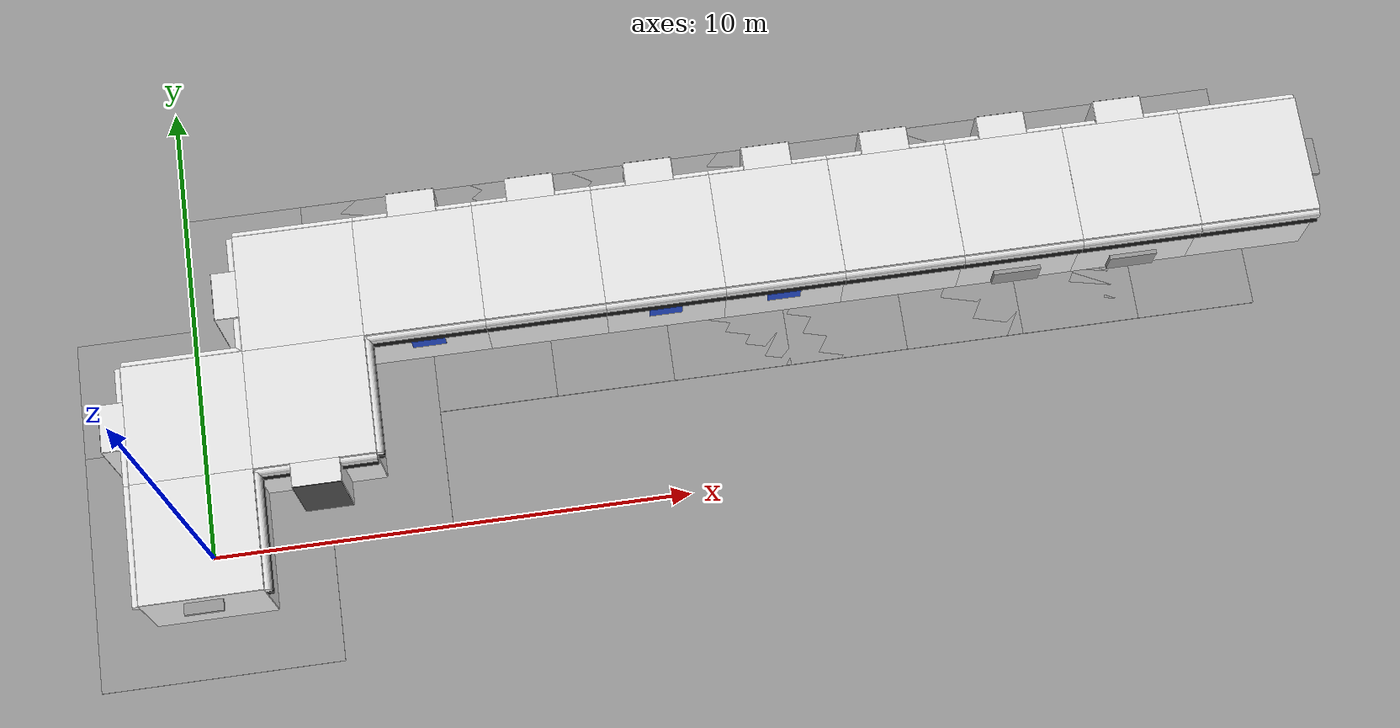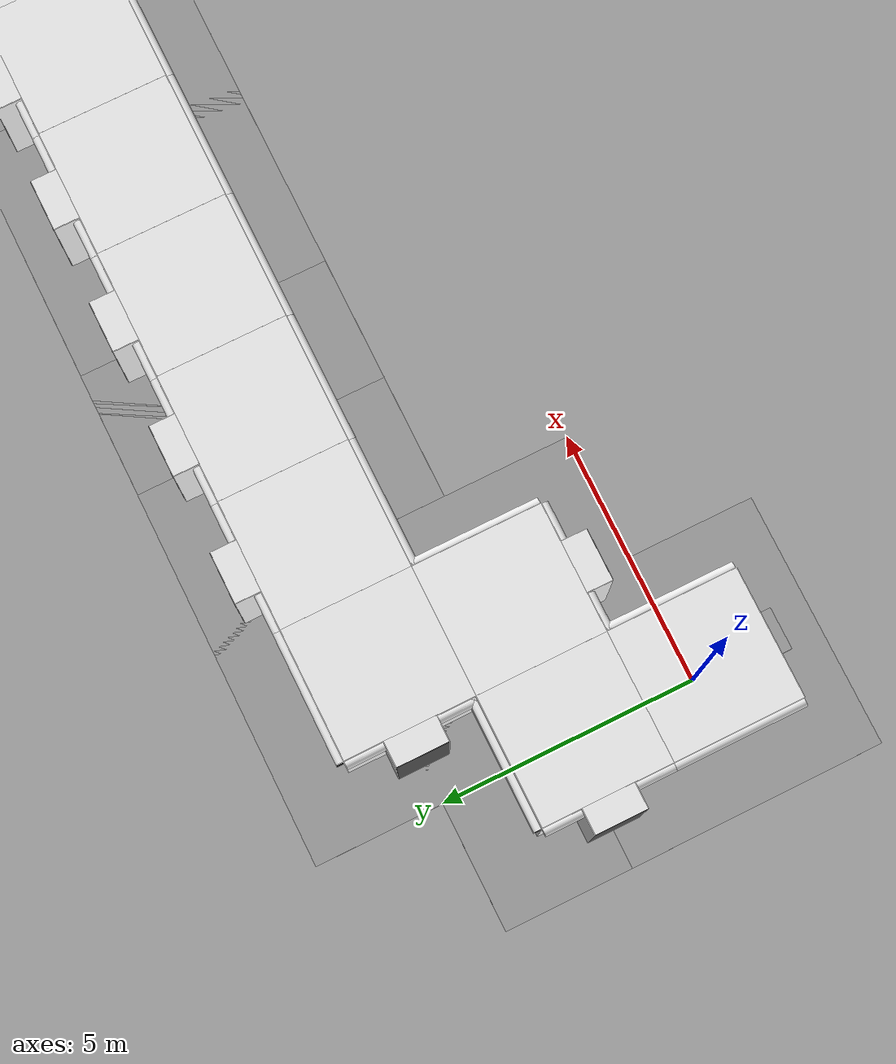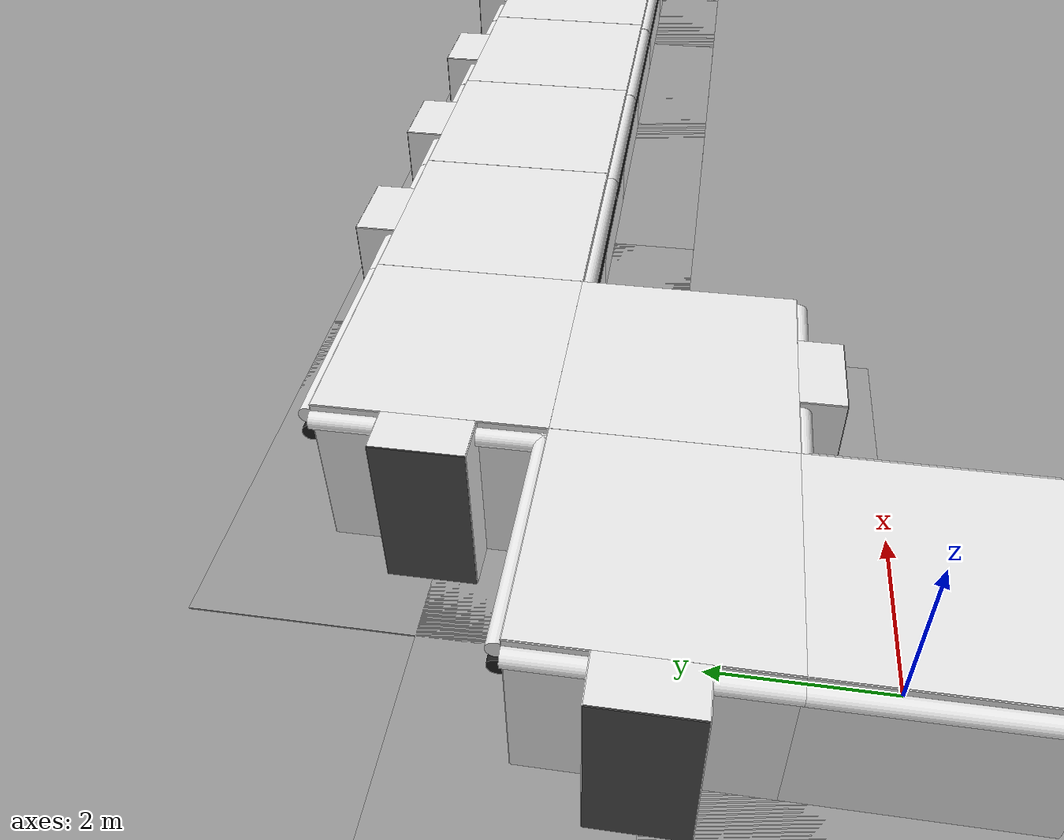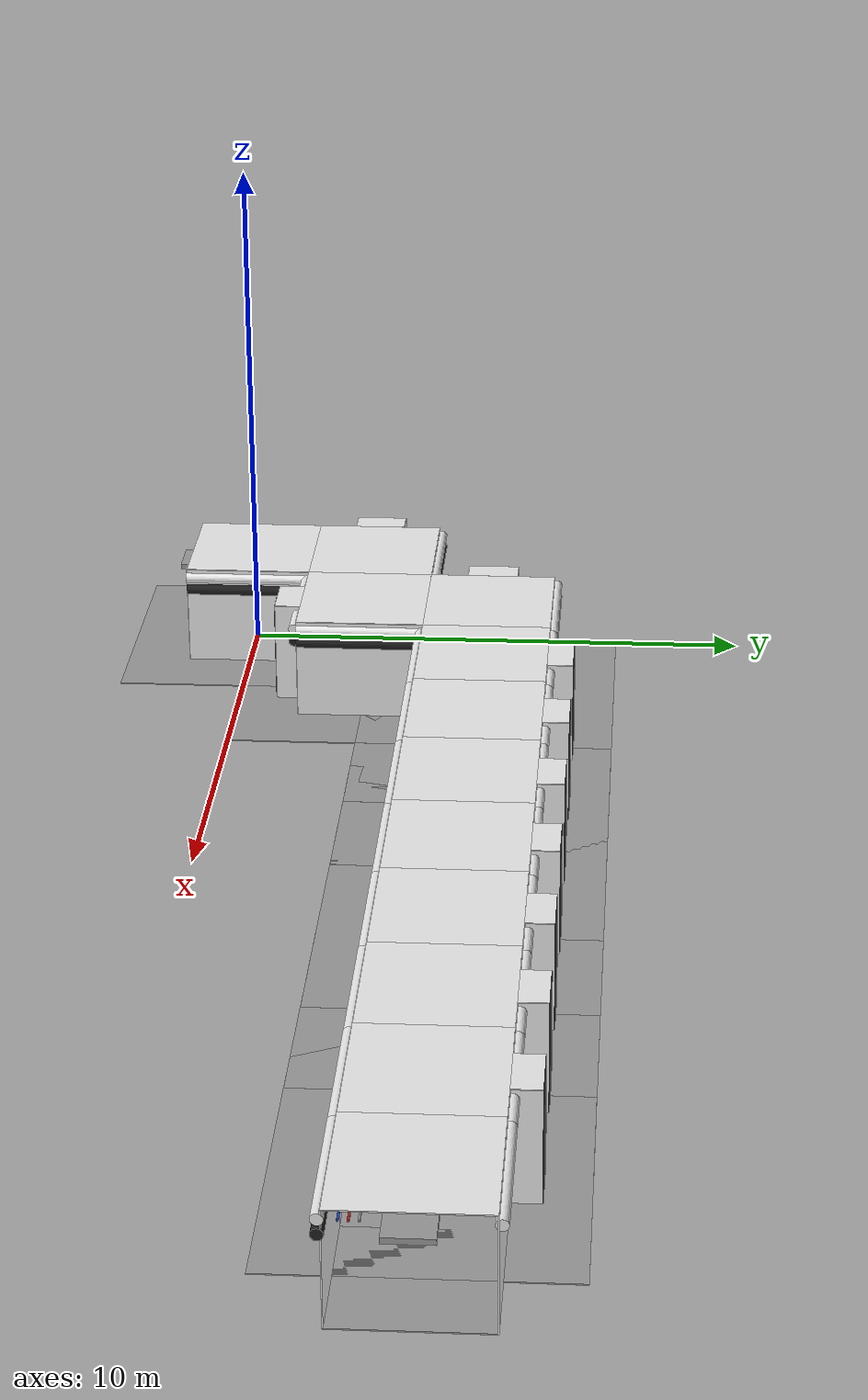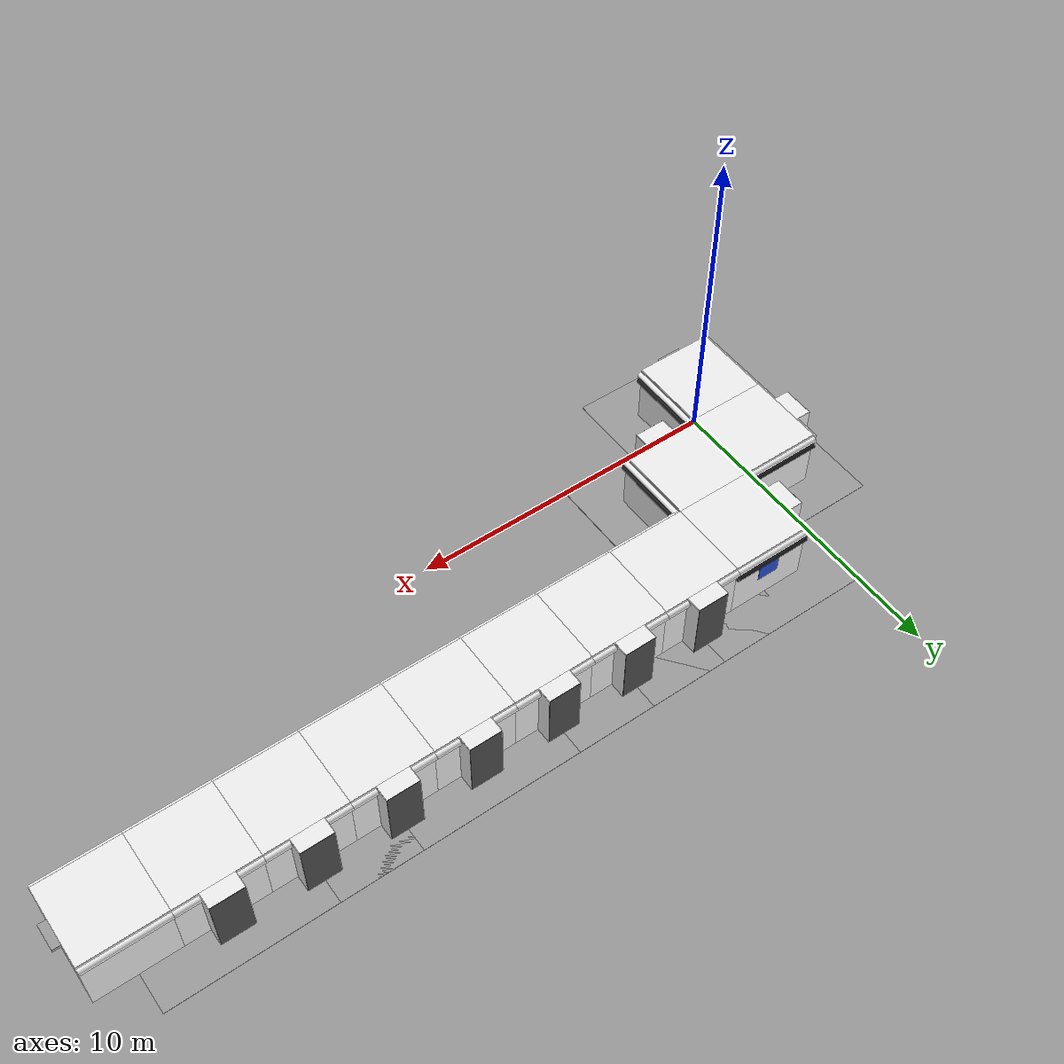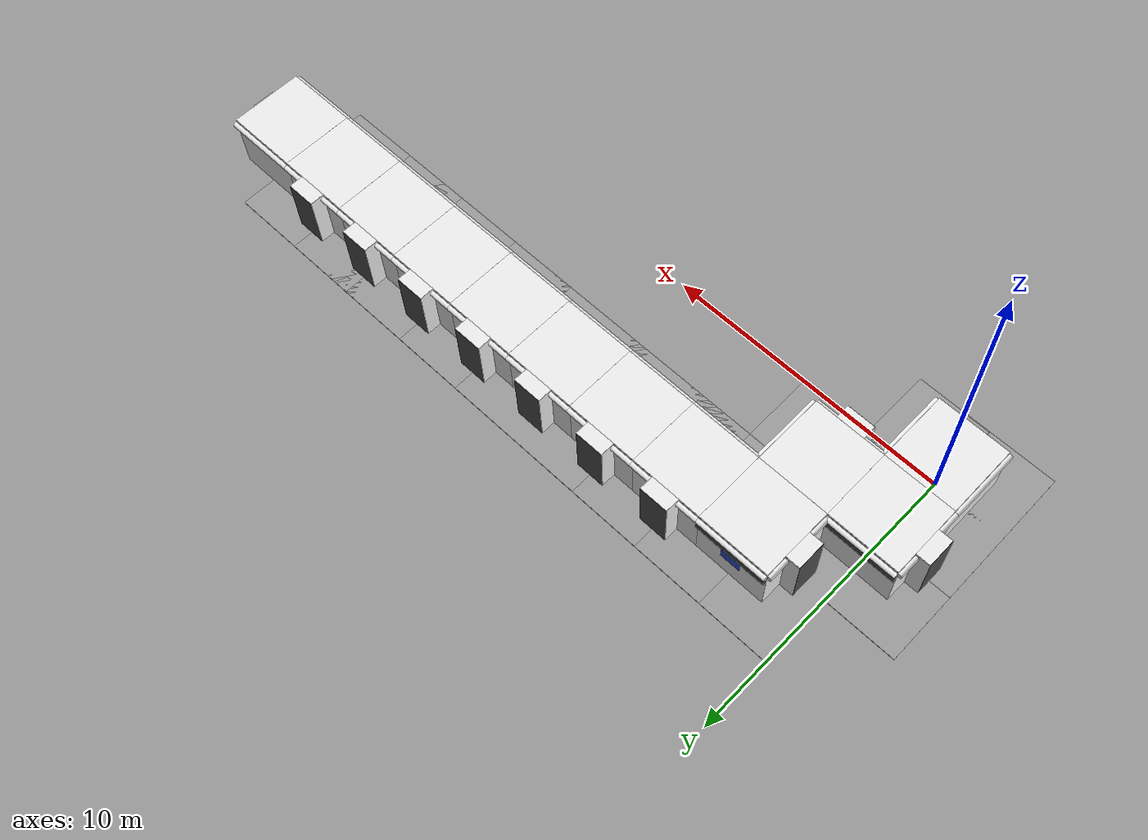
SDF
<sdf version="1.6">
 <world name="default">
  <gravity>0 0 -9.8</gravity>
  <magnetic_field>6e-06 2.3e-05 -4.2e-05</magnetic_field>
  <atmosphere type="adiabatic"/>
  <physics default="0" name="default_physics" type="ode">
   <max_step_size>0.001</max_step_size>
   <real_time_factor>1</real_time_factor>
   <real_time_update_rate>1000</real_time_update_rate>
  </physics>
  <scene><ambient>0.4 0.4 0.4 1</ambient><background>0.7 0.7 0.7 1</background><shadows>0</shadows></scene>
  <spherical_coordinates>
   <surface_model>EARTH_WGS84</surface_model>
   <latitude_deg>0</latitude_deg>
   <longitude_deg>0</longitude_deg>
   <elevation>0</elevation>
   <heading_deg>0</heading_deg>
  </spherical_coordinates>
  <model name="wall_back_0_0_0_0">
   <static>1</static>
   <pose>0.0 -1.25 1.0 0.0 0.0 0.0</pose>
   <link name="link">
    <collision name="collision"><geometry><box><size>2.5 0.02 2.0</size></box></geometry></collision>
    <visual name="visual">
     <material>
      <script><name>Gazebo/White</name><uri>file://media/materials/scripts/gazebo.material</uri></script>
     </material>
     <geometry><box><size>2.5 0.02 2.0</size></box></geometry>
    </visual>
   </link>
  </model>
  <model name="wall_right_0_0_0_0">
   <static>1</static>
   <pose>1.25 0.0 1.0 0.0 0.0 1.57</pose>
   <link name="link">
    <collision name="collision"><geometry><box><size>2.5 0.02 2.0</size></box></geometry></collision>
    <visual name="visual">
     <material>
      <script><name>Gazebo/White</name><uri>file://media/materials/scripts/gazebo.material</uri></script>
     </material>
     <geometry><box><size>2.5 0.02 2.0</size></box></geometry>
    </visual>
   </link>
  </model>
  <model name="wall_left_0_0_0_0">
   <static>1</static>
   <pose>-1.25 0.0 1.0 0.0 0.0 1.57</pose>
   <link name="link">
    <collision name="collision"><geometry><box><size>2.5 0.02 2.0</size></box></geometry></collision>
    <visual name="visual">
     <material>
      <script><name>Gazebo/White</name><uri>file://media/materials/scripts/gazebo.material</uri></script>
     </material>
     <geometry><box><size>2.5 0.02 2.0</size></box></geometry>
    </visual>
   </link>
  </model>
  <model name="wall_top_0_0_0_0">
   <static>1</static>
   <pose>0.0 0.0 2.0 1.57 0.0 0.0</pose>
   <link name="link">
    <collision name="collision"><geometry><box><size>2.5 0.02 2.5</size></box></geometry></collision>
    <visual name="visual">
     <material>
      <script><name>Gazebo/White</name><uri>file://media/materials/scripts/gazebo.material</uri></script>
     </material>
     <geometry><box><size>2.5 0.02 2.5</size></box></geometry>
    </visual>
   </link>
  </model>
  <light name="lightball_0_0_0_0_0" type="point">
   <cast_shadows>0</cast_shadows>
   <pose>-0.25 -0.25 1.99 0.0 0.0 0.0</pose>
   <diffuse>10 10 10 255</diffuse>
   <specular>10 10 10 255</specular>
  </light>
  <light name="lightball_1_0_0_0_0" type="point">
   <cast_shadows>0</cast_shadows>
   <pose>0.25 -0.25 1.99 0.0 0.0 0.0</pose>
   <diffuse>10 10 10 255</diffuse>
   <specular>10 10 10 255</specular>
  </light>
  <light name="lightball_2_0_0_0_0" type="point">
   <cast_shadows>0</cast_shadows>
   <pose>-0.25 0.25 1.99 0.0 0.0 0.0</pose>
   <diffuse>10 10 10 255</diffuse>
   <specular>10 10 10 255</specular>
  </light>
  <light name="lightball_3_0_0_0_0" type="point">
   <cast_shadows>0</cast_shadows>
   <pose>0.25 0.25 1.99 0.0 0.0 0.0</pose>
   <diffuse>10 10 10 255</diffuse>
   <specular>10 10 10 255</specular>
  </light>
  <model name="ceiling_1_0_0_0_0">
   <pose>0.0 0.0 1.7 0.0 0.0 0.0</pose>
   <link name="link_1">
    <visual name="visual">
     <geometry><box><size>0.8 1 0.1</size></box></geometry>
     <material>
      <script><uri>file://media/materials/scripts/gazebo.material</uri><name>Gazebo/Grey</name></script>
     </material>
    </visual>
    <collision name="collision"><geometry><box><size>0.8 1 0.1</size></box></geometry></collision>
   </link>
   <static>1</static>
  </model>
  <model name="ceiling_1_0_0_1_0">
   <pose>0.0 -1.0 1.7 0.0 0.0 0.0</pose>
   <link name="link_1">
    <visual name="visual">
     <geometry><box><size>0.8 1 0.1</size></box></geometry>
     <material>
      <script><uri>file://media/materials/scripts/gazebo.material</uri><name>Gazebo/Grey</name></script>
     </material>
    </visual>
    <collision name="collision"><geometry><box><size>0.8 1 0.1</size></box></geometry></collision>
   </link>
   <static>1</static>
  </model>
  <model name="ceiling_1_0_0_2_0">
   <pose>0.0 1.0 1.7 0.0 0.0 0.0</pose>
   <link name="link_1">
    <visual name="visual">
     <geometry><box><size>0.8 1 0.1</size></box></geometry>
     <material>
      <script><uri>file://media/materials/scripts/gazebo.material</uri><name>Gazebo/Grey</name></script>
     </material>
    </visual>
    <collision name="collision"><geometry><box><size>0.8 1 0.1</size></box></geometry></collision>
   </link>
   <static>1</static>
  </model>
  <model name="white_pipe_left_0_0_0_0">
   <static>1</static>
   <pose>0.0 0.0 1.84 0.0 0.0 0.0</pose>
   <link name="link_0">
    <visual name="visual">
     <pose>-1.3 0 0 1.57 0 0</pose>
     <geometry><cylinder><radius>0.1</radius><length>2.5</length></cylinder></geometry>
     <material>
      <script><uri>file://media/materials/scripts/gazebo.material</uri><name>Gazebo/White</name></script>
     </material>
    </visual>
    <collision name="collision">
     <pose>-1.3 0 0 1.57 0 0</pose>
     <geometry><cylinder><radius>0.1</radius><length>2.5</length></cylinder></geometry>
    </collision>
   </link>
  </model>
  <model name="white_pipe_right_0_0_0_0">
   <static>1</static>
   <pose>0.0 0.0 1.84 0.0 0.0 0.0</pose>
   <link name="link_0">
    <visual name="visual">
     <pose>1.3 0 0 1.57 0 0</pose>
     <geometry><cylinder><radius>0.1</radius><length>2.5</length></cylinder></geometry>
     <material>
      <script><uri>file://media/materials/scripts/gazebo.material</uri><name>Gazebo/White</name></script>
     </material>
    </visual>
    <collision name="collision">
     <pose>1.3 0 0 1.57 0 0</pose>
     <geometry><cylinder><radius>0.1</radius><length>2.5</length></cylinder></geometry>
    </collision>
   </link>
  </model>
  <model name="black_pipe_right_0_0_0_0">
   <static>1</static>
   <pose>0.0 0.0 1.84 0.0 0.0 0.0</pose>
   <link name="link_0">
    <visual name="visual">
     <pose>1.3 0 -0.25 1.57 0 0</pose>
     <geometry><cylinder><radius>0.1</radius><length>2.5</length></cylinder></geometry>
     <material>
      <script><uri>file://media/materials/scripts/gazebo.material</uri><name>Gazebo/Black</name></script>
     </material>
    </visual>
    <collision name="collision">
     <pose>1.3 0 -0.25 1.57 0 0</pose>
     <geometry><cylinder><radius>0.1</radius><length>2.5</length></cylinder></geometry>
    </collision>
   </link>
  </model>
  <model name="grey_pipe_right_0_0_0_0">
   <static>1</static>
   <pose>0.0 0.0 1.84 0.0 0.0 0.0</pose>
   <link name="link_0">
    <visual name="visual">
     <pose>0.7 0 0 1.57 0 0</pose>
     <geometry><cylinder><radius>0.02</radius><length>2.5</length></cylinder></geometry>
     <material>
      <script><uri>file://media/materials/scripts/gazebo.material</uri><name>Gazebo/Grey</name></script>
     </material>
    </visual>
    <collision name="collision">
     <pose>0.7 0 0 1.57 0 0</pose>
     <geometry><cylinder><radius>0.02</radius><length>2.5</length></cylinder></geometry>
    </collision>
   </link>
  </model>
  <model name="red_pipe_right_0_0_0_0">
   <static>1</static>
   <pose>0.0 0.0 1.84 0.0 0.0 0.0</pose>
   <link name="link_0">
    <visual name="visual">
     <pose>0.85 0 0 1.57 0 0</pose>
     <geometry><cylinder><radius>0.02</radius><length>2.5</length></cylinder></geometry>
     <material>
      <script><uri>file://media/materials/scripts/gazebo.material</uri><name>Gazebo/Red</name></script>
     </material>
    </visual>
    <collision name="collision">
     <pose>0.85 0 0 1.57 0 0</pose>
     <geometry><cylinder><radius>0.02</radius><length>2.5</length></cylinder></geometry>
    </collision>
   </link>
  </model>
  <model name="blue_pipe_right_0_0_0_0">
   <static>1</static>
   <pose>0.0 0.0 1.84 0.0 0.0 0.0</pose>
   <link name="link_0">
    <visual name="visual">
     <pose>1 0 0 1.57 0 0</pose>
     <geometry><cylinder><radius>0.02</radius><length>2.5</length></cylinder></geometry>
     <material>
      <script><uri>file://media/materials/scripts/gazebo.material</uri><name>Gazebo/Blue</name></script>
     </material>
    </visual>
    <collision name="collision">
     <pose>1 0 0 1.57 0 0</pose>
     <geometry><cylinder><radius>0.02</radius><length>2.5</length></cylinder></geometry>
    </collision>
   </link>
  </model>
  <model name="wall_bottom_0_0_0_0">
   <static>1</static>
   <link name="link">
    <collision name="collision"><geometry><box><size>5.0 5.0 0.02</size></box></geometry></collision>
    <visual name="visual">
     <material>
      <script><name>Gazebo/Grey</name><uri>file://media/materials/scripts/gazebo.material</uri></script>
     </material>
     <geometry><box><size>5.0 5.0 0.02</size></box></geometry>
    </visual>
   </link>
  </model>
  <model name="wall_front_0_1_0_2">
   <static>1</static>
   <pose>0.0 3.75 1.0 0.0 0.0 0.0</pose>
   <link name="link">
    <collision name="collision"><geometry><box><size>2.5 0.02 2.0</size></box></geometry></collision>
    <visual name="visual">
     <material>
      <script><name>Gazebo/White</name><uri>file://media/materials/scripts/gazebo.material</uri></script>
     </material>
     <geometry><box><size>2.5 0.02 2.0</size></box></geometry>
    </visual>
   </link>
  </model>
  <model name="wall_top_0_1_0_2">
   <static>1</static>
   <pose>0.0 2.5 2.0 1.57 0.0 0.0</pose>
   <link name="link">
    <collision name="collision"><geometry><box><size>2.5 0.02 2.5</size></box></geometry></collision>
    <visual name="visual">
     <material>
      <script><name>Gazebo/White</name><uri>file://media/materials/scripts/gazebo.material</uri></script>
     </material>
     <geometry><box><size>2.5 0.02 2.5</size></box></geometry>
    </visual>
   </link>
  </model>
  <light name="lightball_0_0_1_0_2" type="point">
   <cast_shadows>0</cast_shadows>
   <pose>-0.25 2.25 1.99 0.0 0.0 0.0</pose>
   <diffuse>10 10 10 255</diffuse>
   <specular>10 10 10 255</specular>
  </light>
  <light name="lightball_1_0_1_0_2" type="point">
   <cast_shadows>0</cast_shadows>
   <pose>0.25 2.25 1.99 0.0 0.0 0.0</pose>
   <diffuse>10 10 10 255</diffuse>
   <specular>10 10 10 255</specular>
  </light>
  <light name="lightball_2_0_1_0_2" type="point">
   <cast_shadows>0</cast_shadows>
   <pose>-0.25 2.75 1.99 0.0 0.0 0.0</pose>
   <diffuse>10 10 10 255</diffuse>
   <specular>10 10 10 255</specular>
  </light>
  <light name="lightball_3_0_1_0_2" type="point">
   <cast_shadows>0</cast_shadows>
   <pose>0.25 2.75 1.99 0.0 0.0 0.0</pose>
   <diffuse>10 10 10 255</diffuse>
   <specular>10 10 10 255</specular>
  </light>
  <model name="ceiling_1_0_1_0_2">
   <pose>0.0 1.5 1.7 0.0 0.0 0.0</pose>
   <link name="link_1">
    <visual name="visual">
     <geometry><box><size>0.8 1 0.1</size></box></geometry>
     <material>
      <script><uri>file://media/materials/scripts/gazebo.material</uri><name>Gazebo/Grey</name></script>
     </material>
    </visual>
    <collision name="collision"><geometry><box><size>0.8 1 0.1</size></box></geometry></collision>
   </link>
   <static>1</static>
  </model>
  <model name="ceiling_1_0_1_1_2">
   <pose>1.0 2.5 1.7 0.0 0.0 1.57</pose>
   <link name="link_1">
    <visual name="visual">
     <geometry><box><size>0.8 1 0.1</size></box></geometry>
     <material>
      <script><uri>file://media/materials/scripts/gazebo.material</uri><name>Gazebo/Grey</name></script>
     </material>
    </visual>
    <collision name="collision"><geometry><box><size>0.8 1 0.1</size></box></geometry></collision>
   </link>
   <static>1</static>
  </model>
  <model name="white_pipe_left_0_1_0_2">
   <static>1</static>
   <pose>0.0 2.5 1.84 0.0 0.0 0.0</pose>
   <link name="link_0">
    <visual name="visual">
     <pose>-1.3 0 0 1.57 0 0</pose>
     <geometry><cylinder><radius>0.1</radius><length>2.5</length></cylinder></geometry>
     <material>
      <script><uri>file://media/materials/scripts/gazebo.material</uri><name>Gazebo/White</name></script>
     </material>
    </visual>
    <collision name="collision">
     <pose>-1.3 0 0 1.57 0 0</pose>
     <geometry><cylinder><radius>0.1</radius><length>2.5</length></cylinder></geometry>
    </collision>
   </link>
  </model>
  <model name="white_pipe_right_0_1_0_2">
   <static>1</static>
   <pose>0.0 2.5 1.84 0.0 0.0 0.0</pose>
   <link name="link_0">
    <visual name="visual">
     <pose>1.3 0 0 1.57 0 0</pose>
     <geometry><cylinder><radius>0.1</radius><length>2.5</length></cylinder></geometry>
     <material>
      <script><uri>file://media/materials/scripts/gazebo.material</uri><name>Gazebo/White</name></script>
     </material>
    </visual>
    <collision name="collision">
     <pose>1.3 0 0 1.57 0 0</pose>
     <geometry><cylinder><radius>0.1</radius><length>2.5</length></cylinder></geometry>
    </collision>
   </link>
  </model>
  <model name="black_pipe_right_0_1_0_2">
   <static>1</static>
   <pose>0.0 2.5 1.84 0.0 0.0 0.0</pose>
   <link name="link_0">
    <visual name="visual">
     <pose>1.3 0 -0.25 1.57 0 0</pose>
     <geometry><cylinder><radius>0.1</radius><length>2.5</length></cylinder></geometry>
     <material>
      <script><uri>file://media/materials/scripts/gazebo.material</uri><name>Gazebo/Black</name></script>
     </material>
    </visual>
    <collision name="collision">
     <pose>1.3 0 -0.25 1.57 0 0</pose>
     <geometry><cylinder><radius>0.1</radius><length>2.5</length></cylinder></geometry>
    </collision>
   </link>
  </model>
  <model name="grey_pipe_right_0_1_0_2">
   <static>1</static>
   <pose>0.0 2.5 1.84 0.0 0.0 0.0</pose>
   <link name="link_0">
    <visual name="visual">
     <pose>0.7 0 0 1.57 0 0</pose>
     <geometry><cylinder><radius>0.02</radius><length>2.5</length></cylinder></geometry>
     <material>
      <script><uri>file://media/materials/scripts/gazebo.material</uri><name>Gazebo/Grey</name></script>
     </material>
    </visual>
    <collision name="collision">
     <pose>0.7 0 0 1.57 0 0</pose>
     <geometry><cylinder><radius>0.02</radius><length>2.5</length></cylinder></geometry>
    </collision>
   </link>
  </model>
  <model name="red_pipe_right_0_1_0_2">
   <static>1</static>
   <pose>0.0 2.5 1.84 0.0 0.0 0.0</pose>
   <link name="link_0">
    <visual name="visual">
     <pose>0.85 0 0 1.57 0 0</pose>
     <geometry><cylinder><radius>0.02</radius><length>2.5</length></cylinder></geometry>
     <material>
      <script><uri>file://media/materials/scripts/gazebo.material</uri><name>Gazebo/Red</name></script>
     </material>
    </visual>
    <collision name="collision">
     <pose>0.85 0 0 1.57 0 0</pose>
     <geometry><cylinder><radius>0.02</radius><length>2.5</length></cylinder></geometry>
    </collision>
   </link>
  </model>
  <model name="blue_pipe_right_0_1_0_2">
   <static>1</static>
   <pose>0.0 2.5 1.84 0.0 0.0 0.0</pose>
   <link name="link_0">
    <visual name="visual">
     <pose>1 0 0 1.57 0 0</pose>
     <geometry><cylinder><radius>0.02</radius><length>2.5</length></cylinder></geometry>
     <material>
      <script><uri>file://media/materials/scripts/gazebo.material</uri><name>Gazebo/Blue</name></script>
     </material>
    </visual>
    <collision name="collision">
     <pose>1 0 0 1.57 0 0</pose>
     <geometry><cylinder><radius>0.02</radius><length>2.5</length></cylinder></geometry>
    </collision>
   </link>
  </model>
  <model name="white_pipe_left_1_0_1_0_2">
   <static>1</static>
   <pose>0.0 2.5 1.84 0.0 0.0 1.57</pose>
   <link name="link_0">
    <visual name="visual">
     <pose>-1.3 0 0 1.57 0 0</pose>
     <geometry><cylinder><radius>0.1</radius><length>2.5</length></cylinder></geometry>
     <material>
      <script><uri>file://media/materials/scripts/gazebo.material</uri><name>Gazebo/White</name></script>
     </material>
    </visual>
    <collision name="collision">
     <pose>-1.3 0 0 1.57 0 0</pose>
     <geometry><cylinder><radius>0.1</radius><length>2.5</length></cylinder></geometry>
    </collision>
   </link>
  </model>
  <model name="white_pipe_right_1_0_1_0_2">
   <static>1</static>
   <pose>0.0 2.5 1.84 0.0 0.0 1.57</pose>
   <link name="link_0">
    <visual name="visual">
     <pose>1.3 0 0 1.57 0 0</pose>
     <geometry><cylinder><radius>0.1</radius><length>2.5</length></cylinder></geometry>
     <material>
      <script><uri>file://media/materials/scripts/gazebo.material</uri><name>Gazebo/White</name></script>
     </material>
    </visual>
    <collision name="collision">
     <pose>1.3 0 0 1.57 0 0</pose>
     <geometry><cylinder><radius>0.1</radius><length>2.5</length></cylinder></geometry>
    </collision>
   </link>
  </model>
  <model name="black_pipe_right_1_0_1_0_2">
   <static>1</static>
   <pose>0.0 2.5 1.84 0.0 0.0 1.57</pose>
   <link name="link_0">
    <visual name="visual">
     <pose>1.3 0 -0.25 1.57 0 0</pose>
     <geometry><cylinder><radius>0.1</radius><length>2.5</length></cylinder></geometry>
     <material>
      <script><uri>file://media/materials/scripts/gazebo.material</uri><name>Gazebo/Black</name></script>
     </material>
    </visual>
    <collision name="collision">
     <pose>1.3 0 -0.25 1.57 0 0</pose>
     <geometry><cylinder><radius>0.1</radius><length>2.5</length></cylinder></geometry>
    </collision>
   </link>
  </model>
  <model name="grey_pipe_right_1_0_1_0_2">
   <static>1</static>
   <pose>0.0 2.5 1.84 0.0 0.0 1.57</pose>
   <link name="link_0">
    <visual name="visual">
     <pose>0.7 0 0 1.57 0 0</pose>
     <geometry><cylinder><radius>0.02</radius><length>2.5</length></cylinder></geometry>
     <material>
      <script><uri>file://media/materials/scripts/gazebo.material</uri><name>Gazebo/Grey</name></script>
     </material>
    </visual>
    <collision name="collision">
     <pose>0.7 0 0 1.57 0 0</pose>
     <geometry><cylinder><radius>0.02</radius><length>2.5</length></cylinder></geometry>
    </collision>
   </link>
  </model>
  <model name="red_pipe_right_1_0_1_0_2">
   <static>1</static>
   <pose>0.0 2.5 1.84 0.0 0.0 1.57</pose>
   <link name="link_0">
    <visual name="visual">
     <pose>0.85 0 0 1.57 0 0</pose>
     <geometry><cylinder><radius>0.02</radius><length>2.5</length></cylinder></geometry>
     <material>
      <script><uri>file://media/materials/scripts/gazebo.material</uri><name>Gazebo/Red</name></script>
     </material>
    </visual>
    <collision name="collision">
     <pose>0.85 0 0 1.57 0 0</pose>
     <geometry><cylinder><radius>0.02</radius><length>2.5</length></cylinder></geometry>
    </collision>
   </link>
  </model>
  <model name="blue_pipe_right_1_0_1_0_2">
   <static>1</static>
   <pose>0.0 2.5 1.84 0.0 0.0 1.57</pose>
   <link name="link_0">
    <visual name="visual">
     <pose>1 0 0 1.57 0 0</pose>
     <geometry><cylinder><radius>0.02</radius><length>2.5</length></cylinder></geometry>
     <material>
      <script><uri>file://media/materials/scripts/gazebo.material</uri><name>Gazebo/Blue</name></script>
     </material>
    </visual>
    <collision name="collision">
     <pose>1 0 0 1.57 0 0</pose>
     <geometry><cylinder><radius>0.02</radius><length>2.5</length></cylinder></geometry>
    </collision>
   </link>
  </model>
  <model name="wall_left_front_left_0_1_0_2">
   <static>1</static>
   <pose>-1.25 3.375 1.0 0.0 0.0 1.57</pose>
   <link name="link">
    <collision name="collision"><geometry><box><size>0.75 0.02 2.0</size></box></geometry></collision>
    <visual name="visual">
     <material>
      <script><name>Gazebo/White</name><uri>file://media/materials/scripts/gazebo.material</uri></script>
     </material>
     <geometry><box><size>0.75 0.02 2.0</size></box></geometry>
    </visual>
   </link>
  </model>
  <model name="wall_left_front_right_0_1_0_2">
   <static>1</static>
   <pose>-1.25 1.625 1.0 0.0 0.0 1.57</pose>
   <link name="link">
    <collision name="collision"><geometry><box><size>0.75 0.02 2.0</size></box></geometry></collision>
    <visual name="visual">
     <material>
      <script><name>Gazebo/White</name><uri>file://media/materials/scripts/gazebo.material</uri></script>
     </material>
     <geometry><box><size>0.75 0.02 2.0</size></box></geometry>
    </visual>
   </link>
  </model>
  <model name="wall_left_front_up_0_1_0_2">
   <static>1</static>
   <pose>-1.25 2.5 2.0 0.0 0.0 1.57</pose>
   <link name="link">
    <collision name="collision"><geometry><box><size>1.0 0.02 0.001</size></box></geometry></collision>
    <visual name="visual">
     <material>
      <script><name>Gazebo/White</name><uri>file://media/materials/scripts/gazebo.material</uri></script>
     </material>
     <geometry><box><size>1.0 0.02 0.001</size></box></geometry>
    </visual>
   </link>
  </model>
  <model name="wall_left_inside_back_0_1_0_2">
   <static>1</static>
   <pose>-1.75 2.5 1.0 0.0 0.0 1.57</pose>
   <link name="link">
    <collision name="collision"><geometry><box><size>1 0.02 2</size></box></geometry></collision>
    <visual name="visual">
     <material>
      <script><name>Gazebo/DarkGrey</name><uri>file://media/materials/scripts/gazebo.material</uri></script>
     </material>
     <geometry><box><size>1 0.02 2</size></box></geometry>
    </visual>
   </link>
  </model>
  <model name="wall_left_inside_left_0_1_0_2">
   <static>1</static>
   <pose>-1.5 3.0 1.0 0.0 0.0 0.0</pose>
   <link name="link">
    <collision name="collision"><geometry><box><size>0.5 0.02 2</size></box></geometry></collision>
    <visual name="visual">
     <material>
      <script><name>Gazebo/White</name><uri>file://media/materials/scripts/gazebo.material</uri></script>
     </material>
     <geometry><box><size>0.5 0.02 2</size></box></geometry>
    </visual>
   </link>
  </model>
  <model name="wall_left_inside_right_0_1_0_2">
   <static>1</static>
   <pose>-1.5 2.0 1.0 0.0 0.0 0.0</pose>
   <link name="link">
    <collision name="collision"><geometry><box><size>0.5 0.02 2</size></box></geometry></collision>
    <visual name="visual">
     <material>
      <script><name>Gazebo/White</name><uri>file://media/materials/scripts/gazebo.material</uri></script>
     </material>
     <geometry><box><size>0.5 0.02 2</size></box></geometry>
    </visual>
   </link>
  </model>
  <model name="wall_left_inside_top_0_1_0_2">
   <static>1</static>
   <pose>-1.5 2.5 2.0 1.57 0.0 1.57</pose>
   <link name="link">
    <collision name="collision"><geometry><box><size>1 0.02 0.5</size></box></geometry></collision>
    <visual name="visual">
     <material>
      <script><name>Gazebo/White</name><uri>file://media/materials/scripts/gazebo.material</uri></script>
     </material>
     <geometry><box><size>1 0.02 0.5</size></box></geometry>
    </visual>
   </link>
  </model>
  <model name="wall_bottom_0_1_0_2">
   <static>1</static>
   <pose>0.0 2.5 0.0 0.0 0.0 0.0</pose>
   <link name="link">
    <collision name="collision"><geometry><box><size>5.0 5.0 0.02</size></box></geometry></collision>
    <visual name="visual">
     <material>
      <script><name>Gazebo/Grey</name><uri>file://media/materials/scripts/gazebo.material</uri></script>
     </material>
     <geometry><box><size>5.0 5.0 0.02</size></box></geometry>
    </visual>
   </link>
  </model>
  <model name="wall_front_1_1_0_3">
   <static>1</static>
   <pose>3.75 2.5 1.0 0.0 0.0 -1.57</pose>
   <link name="link">
    <collision name="collision"><geometry><box><size>2.5 0.02 2.0</size></box></geometry></collision>
    <visual name="visual">
     <material>
      <script><name>Gazebo/White</name><uri>file://media/materials/scripts/gazebo.material</uri></script>
     </material>
     <geometry><box><size>2.5 0.02 2.0</size></box></geometry>
    </visual>
   </link>
  </model>
  <model name="wall_top_1_1_0_3">
   <static>1</static>
   <pose>2.5 2.5 2.0 1.57 0.0 -1.57</pose>
   <link name="link">
    <collision name="collision"><geometry><box><size>2.5 0.02 2.5</size></box></geometry></collision>
    <visual name="visual">
     <material>
      <script><name>Gazebo/White</name><uri>file://media/materials/scripts/gazebo.material</uri></script>
     </material>
     <geometry><box><size>2.5 0.02 2.5</size></box></geometry>
    </visual>
   </link>
  </model>
  <light name="lightball_0_1_1_0_3" type="point">
   <cast_shadows>0</cast_shadows>
   <pose>2.25 2.25 1.99 0.0 0.0 0.0</pose>
   <diffuse>10 10 10 255</diffuse>
   <specular>10 10 10 255</specular>
  </light>
  <light name="lightball_1_1_1_0_3" type="point">
   <cast_shadows>0</cast_shadows>
   <pose>2.75 2.25 1.99 0.0 0.0 0.0</pose>
   <diffuse>10 10 10 255</diffuse>
   <specular>10 10 10 255</specular>
  </light>
  <light name="lightball_2_1_1_0_3" type="point">
   <cast_shadows>0</cast_shadows>
   <pose>2.25 2.75 1.99 0.0 0.0 0.0</pose>
   <diffuse>10 10 10 255</diffuse>
   <specular>10 10 10 255</specular>
  </light>
  <light name="lightball_3_1_1_0_3" type="point">
   <cast_shadows>0</cast_shadows>
   <pose>2.75 2.75 1.99 0.0 0.0 0.0</pose>
   <diffuse>10 10 10 255</diffuse>
   <specular>10 10 10 255</specular>
  </light>
  <model name="ceiling_1_1_1_0_3">
   <pose>1.5 2.5 1.7 0.0 0.0 -1.57</pose>
   <link name="link_1">
    <visual name="visual">
     <geometry><box><size>0.8 1 0.1</size></box></geometry>
     <material>
      <script><uri>file://media/materials/scripts/gazebo.material</uri><name>Gazebo/Grey</name></script>
     </material>
    </visual>
    <collision name="collision"><geometry><box><size>0.8 1 0.1</size></box></geometry></collision>
   </link>
   <static>1</static>
  </model>
  <model name="ceiling_1_1_1_1_3">
   <pose>2.5 3.5 1.7 0.0 0.0 0.0</pose>
   <link name="link_1">
    <visual name="visual">
     <geometry><box><size>0.8 1 0.1</size></box></geometry>
     <material>
      <script><uri>file://media/materials/scripts/gazebo.material</uri><name>Gazebo/Grey</name></script>
     </material>
    </visual>
    <collision name="collision"><geometry><box><size>0.8 1 0.1</size></box></geometry></collision>
   </link>
   <static>1</static>
  </model>
  <model name="white_pipe_left_1_1_0_3">
   <static>1</static>
   <pose>2.5 2.5 1.84 0.0 0.0 -1.57</pose>
   <link name="link_0">
    <visual name="visual">
     <pose>-1.3 0 0 1.57 0 0</pose>
     <geometry><cylinder><radius>0.1</radius><length>2.5</length></cylinder></geometry>
     <material>
      <script><uri>file://media/materials/scripts/gazebo.material</uri><name>Gazebo/White</name></script>
     </material>
    </visual>
    <collision name="collision">
     <pose>-1.3 0 0 1.57 0 0</pose>
     <geometry><cylinder><radius>0.1</radius><length>2.5</length></cylinder></geometry>
    </collision>
   </link>
  </model>
  <model name="white_pipe_right_1_1_0_3">
   <static>1</static>
   <pose>2.5 2.5 1.84 0.0 0.0 -1.57</pose>
   <link name="link_0">
    <visual name="visual">
     <pose>1.3 0 0 1.57 0 0</pose>
     <geometry><cylinder><radius>0.1</radius><length>2.5</length></cylinder></geometry>
     <material>
      <script><uri>file://media/materials/scripts/gazebo.material</uri><name>Gazebo/White</name></script>
     </material>
    </visual>
    <collision name="collision">
     <pose>1.3 0 0 1.57 0 0</pose>
     <geometry><cylinder><radius>0.1</radius><length>2.5</length></cylinder></geometry>
    </collision>
   </link>
  </model>
  <model name="black_pipe_right_1_1_0_3">
   <static>1</static>
   <pose>2.5 2.5 1.84 0.0 0.0 -1.57</pose>
   <link name="link_0">
    <visual name="visual">
     <pose>1.3 0 -0.25 1.57 0 0</pose>
     <geometry><cylinder><radius>0.1</radius><length>2.5</length></cylinder></geometry>
     <material>
      <script><uri>file://media/materials/scripts/gazebo.material</uri><name>Gazebo/Black</name></script>
     </material>
    </visual>
    <collision name="collision">
     <pose>1.3 0 -0.25 1.57 0 0</pose>
     <geometry><cylinder><radius>0.1</radius><length>2.5</length></cylinder></geometry>
    </collision>
   </link>
  </model>
  <model name="grey_pipe_right_1_1_0_3">
   <static>1</static>
   <pose>2.5 2.5 1.84 0.0 0.0 -1.57</pose>
   <link name="link_0">
    <visual name="visual">
     <pose>0.7 0 0 1.57 0 0</pose>
     <geometry><cylinder><radius>0.02</radius><length>2.5</length></cylinder></geometry>
     <material>
      <script><uri>file://media/materials/scripts/gazebo.material</uri><name>Gazebo/Grey</name></script>
     </material>
    </visual>
    <collision name="collision">
     <pose>0.7 0 0 1.57 0 0</pose>
     <geometry><cylinder><radius>0.02</radius><length>2.5</length></cylinder></geometry>
    </collision>
   </link>
  </model>
  <model name="red_pipe_right_1_1_0_3">
   <static>1</static>
   <pose>2.5 2.5 1.84 0.0 0.0 -1.57</pose>
   <link name="link_0">
    <visual name="visual">
     <pose>0.85 0 0 1.57 0 0</pose>
     <geometry><cylinder><radius>0.02</radius><length>2.5</length></cylinder></geometry>
     <material>
      <script><uri>file://media/materials/scripts/gazebo.material</uri><name>Gazebo/Red</name></script>
     </material>
    </visual>
    <collision name="collision">
     <pose>0.85 0 0 1.57 0 0</pose>
     <geometry><cylinder><radius>0.02</radius><length>2.5</length></cylinder></geometry>
    </collision>
   </link>
  </model>
  <model name="blue_pipe_right_1_1_0_3">
   <static>1</static>
   <pose>2.5 2.5 1.84 0.0 0.0 -1.57</pose>
   <link name="link_0">
    <visual name="visual">
     <pose>1 0 0 1.57 0 0</pose>
     <geometry><cylinder><radius>0.02</radius><length>2.5</length></cylinder></geometry>
     <material>
      <script><uri>file://media/materials/scripts/gazebo.material</uri><name>Gazebo/Blue</name></script>
     </material>
    </visual>
    <collision name="collision">
     <pose>1 0 0 1.57 0 0</pose>
     <geometry><cylinder><radius>0.02</radius><length>2.5</length></cylinder></geometry>
    </collision>
   </link>
  </model>
  <model name="white_pipe_left_1_1_1_0_3">
   <static>1</static>
   <pose>2.5 2.5 1.84 0.0 0.0 0.0</pose>
   <link name="link_0">
    <visual name="visual">
     <pose>-1.3 0 0 1.57 0 0</pose>
     <geometry><cylinder><radius>0.1</radius><length>2.5</length></cylinder></geometry>
     <material>
      <script><uri>file://media/materials/scripts/gazebo.material</uri><name>Gazebo/White</name></script>
     </material>
    </visual>
    <collision name="collision">
     <pose>-1.3 0 0 1.57 0 0</pose>
     <geometry><cylinder><radius>0.1</radius><length>2.5</length></cylinder></geometry>
    </collision>
   </link>
  </model>
  <model name="white_pipe_right_1_1_1_0_3">
   <static>1</static>
   <pose>2.5 2.5 1.84 0.0 0.0 0.0</pose>
   <link name="link_0">
    <visual name="visual">
     <pose>1.3 0 0 1.57 0 0</pose>
     <geometry><cylinder><radius>0.1</radius><length>2.5</length></cylinder></geometry>
     <material>
      <script><uri>file://media/materials/scripts/gazebo.material</uri><name>Gazebo/White</name></script>
     </material>
    </visual>
    <collision name="collision">
     <pose>1.3 0 0 1.57 0 0</pose>
     <geometry><cylinder><radius>0.1</radius><length>2.5</length></cylinder></geometry>
    </collision>
   </link>
  </model>
  <model name="black_pipe_right_1_1_1_0_3">
   <static>1</static>
   <pose>2.5 2.5 1.84 0.0 0.0 0.0</pose>
   <link name="link_0">
    <visual name="visual">
     <pose>1.3 0 -0.25 1.57 0 0</pose>
     <geometry><cylinder><radius>0.1</radius><length>2.5</length></cylinder></geometry>
     <material>
      <script><uri>file://media/materials/scripts/gazebo.material</uri><name>Gazebo/Black</name></script>
     </material>
    </visual>
    <collision name="collision">
     <pose>1.3 0 -0.25 1.57 0 0</pose>
     <geometry><cylinder><radius>0.1</radius><length>2.5</length></cylinder></geometry>
    </collision>
   </link>
  </model>
  <model name="grey_pipe_right_1_1_1_0_3">
   <static>1</static>
   <pose>2.5 2.5 1.84 0.0 0.0 0.0</pose>
   <link name="link_0">
    <visual name="visual">
     <pose>0.7 0 0 1.57 0 0</pose>
     <geometry><cylinder><radius>0.02</radius><length>2.5</length></cylinder></geometry>
     <material>
      <script><uri>file://media/materials/scripts/gazebo.material</uri><name>Gazebo/Grey</name></script>
     </material>
    </visual>
    <collision name="collision">
     <pose>0.7 0 0 1.57 0 0</pose>
     <geometry><cylinder><radius>0.02</radius><length>2.5</length></cylinder></geometry>
    </collision>
   </link>
  </model>
  <model name="red_pipe_right_1_1_1_0_3">
   <static>1</static>
   <pose>2.5 2.5 1.84 0.0 0.0 0.0</pose>
   <link name="link_0">
    <visual name="visual">
     <pose>0.85 0 0 1.57 0 0</pose>
     <geometry><cylinder><radius>0.02</radius><length>2.5</length></cylinder></geometry>
     <material>
      <script><uri>file://media/materials/scripts/gazebo.material</uri><name>Gazebo/Red</name></script>
     </material>
    </visual>
    <collision name="collision">
     <pose>0.85 0 0 1.57 0 0</pose>
     <geometry><cylinder><radius>0.02</radius><length>2.5</length></cylinder></geometry>
    </collision>
   </link>
  </model>
  <model name="blue_pipe_right_1_1_1_0_3">
   <static>1</static>
   <pose>2.5 2.5 1.84 0.0 0.0 0.0</pose>
   <link name="link_0">
    <visual name="visual">
     <pose>1 0 0 1.57 0 0</pose>
     <geometry><cylinder><radius>0.02</radius><length>2.5</length></cylinder></geometry>
     <material>
      <script><uri>file://media/materials/scripts/gazebo.material</uri><name>Gazebo/Blue</name></script>
     </material>
    </visual>
    <collision name="collision">
     <pose>1 0 0 1.57 0 0</pose>
     <geometry><cylinder><radius>0.02</radius><length>2.5</length></cylinder></geometry>
    </collision>
   </link>
  </model>
  <model name="wall_right_front_left_1_1_0_3">
   <static>1</static>
   <pose>3.375 1.25 1.0 0.0 0.0 0.0</pose>
   <link name="link">
    <collision name="collision"><geometry><box><size>0.75 0.02 2.0</size></box></geometry></collision>
    <visual name="visual">
     <material>
      <script><name>Gazebo/White</name><uri>file://media/materials/scripts/gazebo.material</uri></script>
     </material>
     <geometry><box><size>0.75 0.02 2.0</size></box></geometry>
    </visual>
   </link>
  </model>
  <model name="wall_right_front_right_1_1_0_3">
   <static>1</static>
   <pose>1.625 1.25 1.0 0.0 0.0 0.0</pose>
   <link name="link">
    <collision name="collision"><geometry><box><size>0.75 0.02 2.0</size></box></geometry></collision>
    <visual name="visual">
     <material>
      <script><name>Gazebo/White</name><uri>file://media/materials/scripts/gazebo.material</uri></script>
     </material>
     <geometry><box><size>0.75 0.02 2.0</size></box></geometry>
    </visual>
   </link>
  </model>
  <model name="wall_right_front_up_1_1_0_3">
   <static>1</static>
   <pose>2.5 1.25 2.0 0.0 0.0 0.0</pose>
   <link name="link">
    <collision name="collision"><geometry><box><size>1.0 0.02 0.001</size></box></geometry></collision>
    <visual name="visual">
     <material>
      <script><name>Gazebo/White</name><uri>file://media/materials/scripts/gazebo.material</uri></script>
     </material>
     <geometry><box><size>1.0 0.02 0.001</size></box></geometry>
    </visual>
   </link>
  </model>
  <model name="wall_right_inside_back_1_1_0_3">
   <static>1</static>
   <pose>2.5 0.75 1.0 0.0 0.0 0.0</pose>
   <link name="link">
    <collision name="collision"><geometry><box><size>1 0.02 2</size></box></geometry></collision>
    <visual name="visual">
     <material>
      <script><name>Gazebo/DarkGrey</name><uri>file://media/materials/scripts/gazebo.material</uri></script>
     </material>
     <geometry><box><size>1 0.02 2</size></box></geometry>
    </visual>
   </link>
  </model>
  <model name="wall_right_inside_left_1_1_0_3">
   <static>1</static>
   <pose>3.0 1.0 1.0 0.0 0.0 -1.57</pose>
   <link name="link">
    <collision name="collision"><geometry><box><size>0.5 0.02 2</size></box></geometry></collision>
    <visual name="visual">
     <material>
      <script><name>Gazebo/White</name><uri>file://media/materials/scripts/gazebo.material</uri></script>
     </material>
     <geometry><box><size>0.5 0.02 2</size></box></geometry>
    </visual>
   </link>
  </model>
  <model name="wall_right_inside_right_1_1_0_3">
   <static>1</static>
   <pose>2.0 1.0 1.0 0.0 0.0 -1.57</pose>
   <link name="link">
    <collision name="collision"><geometry><box><size>0.5 0.02 2</size></box></geometry></collision>
    <visual name="visual">
     <material>
      <script><name>Gazebo/White</name><uri>file://media/materials/scripts/gazebo.material</uri></script>
     </material>
     <geometry><box><size>0.5 0.02 2</size></box></geometry>
    </visual>
   </link>
  </model>
  <model name="wall_right_inside_top_1_1_0_3">
   <static>1</static>
   <pose>2.5 1.0 2.0 1.57 0.0 0.0</pose>
   <link name="link">
    <collision name="collision"><geometry><box><size>1 0.02 0.5</size></box></geometry></collision>
    <visual name="visual">
     <material>
      <script><name>Gazebo/White</name><uri>file://media/materials/scripts/gazebo.material</uri></script>
     </material>
     <geometry><box><size>1 0.02 0.5</size></box></geometry>
    </visual>
   </link>
  </model>
  <model name="wall_bottom_1_1_0_3">
   <static>1</static>
   <pose>2.5 2.5 0.0 0.0 0.0 -1.57</pose>
   <link name="link">
    <collision name="collision"><geometry><box><size>5.0 5.0 0.02</size></box></geometry></collision>
    <visual name="visual">
     <material>
      <script><name>Gazebo/Grey</name><uri>file://media/materials/scripts/gazebo.material</uri></script>
     </material>
     <geometry><box><size>5.0 5.0 0.02</size></box></geometry>
    </visual>
   </link>
  </model>
  <model name="wall_front_1_2_0_2">
   <static>1</static>
   <pose>2.5 6.25 1.0 0.0 0.0 0.0</pose>
   <link name="link">
    <collision name="collision"><geometry><box><size>2.5 0.02 2.0</size></box></geometry></collision>
    <visual name="visual">
     <material>
      <script><name>Gazebo/White</name><uri>file://media/materials/scripts/gazebo.material</uri></script>
     </material>
     <geometry><box><size>2.5 0.02 2.0</size></box></geometry>
    </visual>
   </link>
  </model>
  <model name="wall_top_1_2_0_2">
   <static>1</static>
   <pose>2.5 5.0 2.0 1.57 0.0 0.0</pose>
   <link name="link">
    <collision name="collision"><geometry><box><size>2.5 0.02 2.5</size></box></geometry></collision>
    <visual name="visual">
     <material>
      <script><name>Gazebo/White</name><uri>file://media/materials/scripts/gazebo.material</uri></script>
     </material>
     <geometry><box><size>2.5 0.02 2.5</size></box></geometry>
    </visual>
   </link>
  </model>
  <light name="lightball_0_1_2_0_2" type="point">
   <cast_shadows>0</cast_shadows>
   <pose>2.25 4.75 1.99 0.0 0.0 0.0</pose>
   <diffuse>10 10 10 255</diffuse>
   <specular>10 10 10 255</specular>
  </light>
  <light name="lightball_1_1_2_0_2" type="point">
   <cast_shadows>0</cast_shadows>
   <pose>2.75 4.75 1.99 0.0 0.0 0.0</pose>
   <diffuse>10 10 10 255</diffuse>
   <specular>10 10 10 255</specular>
  </light>
  <light name="lightball_2_1_2_0_2" type="point">
   <cast_shadows>0</cast_shadows>
   <pose>2.25 5.25 1.99 0.0 0.0 0.0</pose>
   <diffuse>10 10 10 255</diffuse>
   <specular>10 10 10 255</specular>
  </light>
  <light name="lightball_3_1_2_0_2" type="point">
   <cast_shadows>0</cast_shadows>
   <pose>2.75 5.25 1.99 0.0 0.0 0.0</pose>
   <diffuse>10 10 10 255</diffuse>
   <specular>10 10 10 255</specular>
  </light>
  <model name="ceiling_1_1_2_0_2">
   <pose>2.5 4.0 1.7 0.0 0.0 0.0</pose>
   <link name="link_1">
    <visual name="visual">
     <geometry><box><size>0.8 1 0.1</size></box></geometry>
     <material>
      <script><uri>file://media/materials/scripts/gazebo.material</uri><name>Gazebo/Grey</name></script>
     </material>
    </visual>
    <collision name="collision"><geometry><box><size>0.8 1 0.1</size></box></geometry></collision>
   </link>
   <static>1</static>
  </model>
  <model name="ceiling_1_1_2_1_2">
   <pose>3.5 5.0 1.7 0.0 0.0 1.57</pose>
   <link name="link_1">
    <visual name="visual">
     <geometry><box><size>0.8 1 0.1</size></box></geometry>
     <material>
      <script><uri>file://media/materials/scripts/gazebo.material</uri><name>Gazebo/Grey</name></script>
     </material>
    </visual>
    <collision name="collision"><geometry><box><size>0.8 1 0.1</size></box></geometry></collision>
   </link>
   <static>1</static>
  </model>
  <model name="white_pipe_left_1_2_0_2">
   <static>1</static>
   <pose>2.5 5.0 1.84 0.0 0.0 0.0</pose>
   <link name="link_0">
    <visual name="visual">
     <pose>-1.3 0 0 1.57 0 0</pose>
     <geometry><cylinder><radius>0.1</radius><length>2.5</length></cylinder></geometry>
     <material>
      <script><uri>file://media/materials/scripts/gazebo.material</uri><name>Gazebo/White</name></script>
     </material>
    </visual>
    <collision name="collision">
     <pose>-1.3 0 0 1.57 0 0</pose>
     <geometry><cylinder><radius>0.1</radius><length>2.5</length></cylinder></geometry>
    </collision>
   </link>
  </model>
  <model name="white_pipe_right_1_2_0_2">
   <static>1</static>
   <pose>2.5 5.0 1.84 0.0 0.0 0.0</pose>
   <link name="link_0">
    <visual name="visual">
     <pose>1.3 0 0 1.57 0 0</pose>
     <geometry><cylinder><radius>0.1</radius><length>2.5</length></cylinder></geometry>
     <material>
      <script><uri>file://media/materials/scripts/gazebo.material</uri><name>Gazebo/White</name></script>
     </material>
    </visual>
    <collision name="collision">
     <pose>1.3 0 0 1.57 0 0</pose>
     <geometry><cylinder><radius>0.1</radius><length>2.5</length></cylinder></geometry>
    </collision>
   </link>
  </model>
  <model name="black_pipe_right_1_2_0_2">
   <static>1</static>
   <pose>2.5 5.0 1.84 0.0 0.0 0.0</pose>
   <link name="link_0">
    <visual name="visual">
     <pose>1.3 0 -0.25 1.57 0 0</pose>
     <geometry><cylinder><radius>0.1</radius><length>2.5</length></cylinder></geometry>
     <material>
      <script><uri>file://media/materials/scripts/gazebo.material</uri><name>Gazebo/Black</name></script>
     </material>
    </visual>
    <collision name="collision">
     <pose>1.3 0 -0.25 1.57 0 0</pose>
     <geometry><cylinder><radius>0.1</radius><length>2.5</length></cylinder></geometry>
    </collision>
   </link>
  </model>
  <model name="grey_pipe_right_1_2_0_2">
   <static>1</static>
   <pose>2.5 5.0 1.84 0.0 0.0 0.0</pose>
   <link name="link_0">
    <visual name="visual">
     <pose>0.7 0 0 1.57 0 0</pose>
     <geometry><cylinder><radius>0.02</radius><length>2.5</length></cylinder></geometry>
     <material>
      <script><uri>file://media/materials/scripts/gazebo.material</uri><name>Gazebo/Grey</name></script>
     </material>
    </visual>
    <collision name="collision">
     <pose>0.7 0 0 1.57 0 0</pose>
     <geometry><cylinder><radius>0.02</radius><length>2.5</length></cylinder></geometry>
    </collision>
   </link>
  </model>
  <model name="red_pipe_right_1_2_0_2">
   <static>1</static>
   <pose>2.5 5.0 1.84 0.0 0.0 0.0</pose>
   <link name="link_0">
    <visual name="visual">
     <pose>0.85 0 0 1.57 0 0</pose>
     <geometry><cylinder><radius>0.02</radius><length>2.5</length></cylinder></geometry>
     <material>
      <script><uri>file://media/materials/scripts/gazebo.material</uri><name>Gazebo/Red</name></script>
     </material>
    </visual>
    <collision name="collision">
     <pose>0.85 0 0 1.57 0 0</pose>
     <geometry><cylinder><radius>0.02</radius><length>2.5</length></cylinder></geometry>
    </collision>
   </link>
  </model>
  <model name="blue_pipe_right_1_2_0_2">
   <static>1</static>
   <pose>2.5 5.0 1.84 0.0 0.0 0.0</pose>
   <link name="link_0">
    <visual name="visual">
     <pose>1 0 0 1.57 0 0</pose>
     <geometry><cylinder><radius>0.02</radius><length>2.5</length></cylinder></geometry>
     <material>
      <script><uri>file://media/materials/scripts/gazebo.material</uri><name>Gazebo/Blue</name></script>
     </material>
    </visual>
    <collision name="collision">
     <pose>1 0 0 1.57 0 0</pose>
     <geometry><cylinder><radius>0.02</radius><length>2.5</length></cylinder></geometry>
    </collision>
   </link>
  </model>
  <model name="white_pipe_left_1_1_2_0_2">
   <static>1</static>
   <pose>2.5 5.0 1.84 0.0 0.0 1.57</pose>
   <link name="link_0">
    <visual name="visual">
     <pose>-1.3 0 0 1.57 0 0</pose>
     <geometry><cylinder><radius>0.1</radius><length>2.5</length></cylinder></geometry>
     <material>
      <script><uri>file://media/materials/scripts/gazebo.material</uri><name>Gazebo/White</name></script>
     </material>
    </visual>
    <collision name="collision">
     <pose>-1.3 0 0 1.57 0 0</pose>
     <geometry><cylinder><radius>0.1</radius><length>2.5</length></cylinder></geometry>
    </collision>
   </link>
  </model>
  <model name="white_pipe_right_1_1_2_0_2">
   <static>1</static>
   <pose>2.5 5.0 1.84 0.0 0.0 1.57</pose>
   <link name="link_0">
    <visual name="visual">
     <pose>1.3 0 0 1.57 0 0</pose>
     <geometry><cylinder><radius>0.1</radius><length>2.5</length></cylinder></geometry>
     <material>
      <script><uri>file://media/materials/scripts/gazebo.material</uri><name>Gazebo/White</name></script>
     </material>
    </visual>
    <collision name="collision">
     <pose>1.3 0 0 1.57 0 0</pose>
     <geometry><cylinder><radius>0.1</radius><length>2.5</length></cylinder></geometry>
    </collision>
   </link>
  </model>
  <model name="black_pipe_right_1_1_2_0_2">
   <static>1</static>
   <pose>2.5 5.0 1.84 0.0 0.0 1.57</pose>
   <link name="link_0">
    <visual name="visual">
     <pose>1.3 0 -0.25 1.57 0 0</pose>
     <geometry><cylinder><radius>0.1</radius><length>2.5</length></cylinder></geometry>
     <material>
      <script><uri>file://media/materials/scripts/gazebo.material</uri><name>Gazebo/Black</name></script>
     </material>
    </visual>
    <collision name="collision">
     <pose>1.3 0 -0.25 1.57 0 0</pose>
     <geometry><cylinder><radius>0.1</radius><length>2.5</length></cylinder></geometry>
    </collision>
   </link>
  </model>
  <model name="grey_pipe_right_1_1_2_0_2">
   <static>1</static>
   <pose>2.5 5.0 1.84 0.0 0.0 1.57</pose>
   <link name="link_0">
    <visual name="visual">
     <pose>0.7 0 0 1.57 0 0</pose>
     <geometry><cylinder><radius>0.02</radius><length>2.5</length></cylinder></geometry>
     <material>
      <script><uri>file://media/materials/scripts/gazebo.material</uri><name>Gazebo/Grey</name></script>
     </material>
    </visual>
    <collision name="collision">
     <pose>0.7 0 0 1.57 0 0</pose>
     <geometry><cylinder><radius>0.02</radius><length>2.5</length></cylinder></geometry>
    </collision>
   </link>
  </model>
  <model name="red_pipe_right_1_1_2_0_2">
   <static>1</static>
   <pose>2.5 5.0 1.84 0.0 0.0 1.57</pose>
   <link name="link_0">
    <visual name="visual">
     <pose>0.85 0 0 1.57 0 0</pose>
     <geometry><cylinder><radius>0.02</radius><length>2.5</length></cylinder></geometry>
     <material>
      <script><uri>file://media/materials/scripts/gazebo.material</uri><name>Gazebo/Red</name></script>
     </material>
    </visual>
    <collision name="collision">
     <pose>0.85 0 0 1.57 0 0</pose>
     <geometry><cylinder><radius>0.02</radius><length>2.5</length></cylinder></geometry>
    </collision>
   </link>
  </model>
  <model name="blue_pipe_right_1_1_2_0_2">
   <static>1</static>
   <pose>2.5 5.0 1.84 0.0 0.0 1.57</pose>
   <link name="link_0">
    <visual name="visual">
     <pose>1 0 0 1.57 0 0</pose>
     <geometry><cylinder><radius>0.02</radius><length>2.5</length></cylinder></geometry>
     <material>
      <script><uri>file://media/materials/scripts/gazebo.material</uri><name>Gazebo/Blue</name></script>
     </material>
    </visual>
    <collision name="collision">
     <pose>1 0 0 1.57 0 0</pose>
     <geometry><cylinder><radius>0.02</radius><length>2.5</length></cylinder></geometry>
    </collision>
   </link>
  </model>
  <model name="panel_1_2_0_2">
   <static>1</static>
   <pose>2.5 6.25 1.3 0.0 0.0 1.57</pose>
   <link name="link">
    <collision name="collision"><geometry><box><size>0.04 0.7 1</size></box></geometry></collision>
    <visual name="visual">
     <material>
      <script><name>Gazebo/Blue</name><uri>file://media/materials/scripts/gazebo.material</uri></script>
     </material>
     <geometry><box><size>0.04 0.7 1</size></box></geometry>
    </visual>
   </link>
  </model>
  <model name="wall_left_front_left_1_2_0_2">
   <static>1</static>
   <pose>1.25 5.875 1.0 0.0 0.0 1.57</pose>
   <link name="link">
    <collision name="collision"><geometry><box><size>0.75 0.02 2.0</size></box></geometry></collision>
    <visual name="visual">
     <material>
      <script><name>Gazebo/White</name><uri>file://media/materials/scripts/gazebo.material</uri></script>
     </material>
     <geometry><box><size>0.75 0.02 2.0</size></box></geometry>
    </visual>
   </link>
  </model>
  <model name="wall_left_front_right_1_2_0_2">
   <static>1</static>
   <pose>1.25 4.125 1.0 0.0 0.0 1.57</pose>
   <link name="link">
    <collision name="collision"><geometry><box><size>0.75 0.02 2.0</size></box></geometry></collision>
    <visual name="visual">
     <material>
      <script><name>Gazebo/White</name><uri>file://media/materials/scripts/gazebo.material</uri></script>
     </material>
     <geometry><box><size>0.75 0.02 2.0</size></box></geometry>
    </visual>
   </link>
  </model>
  <model name="wall_left_front_up_1_2_0_2">
   <static>1</static>
   <pose>1.25 5.0 2.0 0.0 0.0 1.57</pose>
   <link name="link">
    <collision name="collision"><geometry><box><size>1.0 0.02 0.001</size></box></geometry></collision>
    <visual name="visual">
     <material>
      <script><name>Gazebo/White</name><uri>file://media/materials/scripts/gazebo.material</uri></script>
     </material>
     <geometry><box><size>1.0 0.02 0.001</size></box></geometry>
    </visual>
   </link>
  </model>
  <model name="wall_left_inside_back_1_2_0_2">
   <static>1</static>
   <pose>0.75 5.0 1.0 0.0 0.0 1.57</pose>
   <link name="link">
    <collision name="collision"><geometry><box><size>1 0.02 2</size></box></geometry></collision>
    <visual name="visual">
     <material>
      <script><name>Gazebo/DarkGrey</name><uri>file://media/materials/scripts/gazebo.material</uri></script>
     </material>
     <geometry><box><size>1 0.02 2</size></box></geometry>
    </visual>
   </link>
  </model>
  <model name="wall_left_inside_left_1_2_0_2">
   <static>1</static>
   <pose>1.0 5.5 1.0 0.0 0.0 0.0</pose>
   <link name="link">
    <collision name="collision"><geometry><box><size>0.5 0.02 2</size></box></geometry></collision>
    <visual name="visual">
     <material>
      <script><name>Gazebo/White</name><uri>file://media/materials/scripts/gazebo.material</uri></script>
     </material>
     <geometry><box><size>0.5 0.02 2</size></box></geometry>
    </visual>
   </link>
  </model>
  <model name="wall_left_inside_right_1_2_0_2">
   <static>1</static>
   <pose>1.0 4.5 1.0 0.0 0.0 0.0</pose>
   <link name="link">
    <collision name="collision"><geometry><box><size>0.5 0.02 2</size></box></geometry></collision>
    <visual name="visual">
     <material>
      <script><name>Gazebo/White</name><uri>file://media/materials/scripts/gazebo.material</uri></script>
     </material>
     <geometry><box><size>0.5 0.02 2</size></box></geometry>
    </visual>
   </link>
  </model>
  <model name="wall_left_inside_top_1_2_0_2">
   <static>1</static>
   <pose>1.0 5.0 2.0 1.57 0.0 1.57</pose>
   <link name="link">
    <collision name="collision"><geometry><box><size>1 0.02 0.5</size></box></geometry></collision>
    <visual name="visual">
     <material>
      <script><name>Gazebo/White</name><uri>file://media/materials/scripts/gazebo.material</uri></script>
     </material>
     <geometry><box><size>1 0.02 0.5</size></box></geometry>
    </visual>
   </link>
  </model>
  <model name="wall_bottom_1_2_0_2">
   <static>1</static>
   <pose>2.5 5.0 0.0 0.0 0.0 0.0</pose>
   <link name="link">
    <collision name="collision"><geometry><box><size>5.0 5.0 0.02</size></box></geometry></collision>
    <visual name="visual">
     <material>
      <script><name>Gazebo/Grey</name><uri>file://media/materials/scripts/gazebo.material</uri></script>
     </material>
     <geometry><box><size>5.0 5.0 0.02</size></box></geometry>
    </visual>
   </link>
  </model>
  <model name="wall_right_2_2_0_1">
   <static>1</static>
   <pose>5.0 3.75 1.0 0.0 0.0 0.0</pose>
   <link name="link">
    <collision name="collision"><geometry><box><size>2.5 0.02 2.0</size></box></geometry></collision>
    <visual name="visual">
     <material>
      <script><name>Gazebo/White</name><uri>file://media/materials/scripts/gazebo.material</uri></script>
     </material>
     <geometry><box><size>2.5 0.02 2.0</size></box></geometry>
    </visual>
   </link>
  </model>
  <model name="wall_top_2_2_0_1">
   <static>1</static>
   <pose>5.0 5.0 2.0 1.57 0.0 -1.57</pose>
   <link name="link">
    <collision name="collision"><geometry><box><size>2.5 0.02 2.5</size></box></geometry></collision>
    <visual name="visual">
     <material>
      <script><name>Gazebo/White</name><uri>file://media/materials/scripts/gazebo.material</uri></script>
     </material>
     <geometry><box><size>2.5 0.02 2.5</size></box></geometry>
    </visual>
   </link>
  </model>
  <light name="lightball_0_2_2_0_1" type="point">
   <cast_shadows>0</cast_shadows>
   <pose>4.75 4.75 1.99 0.0 0.0 0.0</pose>
   <diffuse>10 10 10 255</diffuse>
   <specular>10 10 10 255</specular>
  </light>
  <light name="lightball_1_2_2_0_1" type="point">
   <cast_shadows>0</cast_shadows>
   <pose>5.25 4.75 1.99 0.0 0.0 0.0</pose>
   <diffuse>10 10 10 255</diffuse>
   <specular>10 10 10 255</specular>
  </light>
  <light name="lightball_2_2_2_0_1" type="point">
   <cast_shadows>0</cast_shadows>
   <pose>4.75 5.25 1.99 0.0 0.0 0.0</pose>
   <diffuse>10 10 10 255</diffuse>
   <specular>10 10 10 255</specular>
  </light>
  <light name="lightball_3_2_2_0_1" type="point">
   <cast_shadows>0</cast_shadows>
   <pose>5.25 5.25 1.99 0.0 0.0 0.0</pose>
   <diffuse>10 10 10 255</diffuse>
   <specular>10 10 10 255</specular>
  </light>
  <model name="ceiling_1_2_2_0_1">
   <pose>5.0 5.0 1.7 0.0 0.0 -1.57</pose>
   <link name="link_1">
    <visual name="visual">
     <geometry><box><size>0.8 1 0.1</size></box></geometry>
     <material>
      <script><uri>file://media/materials/scripts/gazebo.material</uri><name>Gazebo/Grey</name></script>
     </material>
    </visual>
    <collision name="collision"><geometry><box><size>0.8 1 0.1</size></box></geometry></collision>
   </link>
   <static>1</static>
  </model>
  <model name="ceiling_1_2_2_1_1">
   <pose>4.0 5.0 1.7 0.0 0.0 -1.57</pose>
   <link name="link_1">
    <visual name="visual">
     <geometry><box><size>0.8 1 0.1</size></box></geometry>
     <material>
      <script><uri>file://media/materials/scripts/gazebo.material</uri><name>Gazebo/Grey</name></script>
     </material>
    </visual>
    <collision name="collision"><geometry><box><size>0.8 1 0.1</size></box></geometry></collision>
   </link>
   <static>1</static>
  </model>
  <model name="ceiling_1_2_2_2_1">
   <pose>6.0 5.0 1.7 0.0 0.0 -1.57</pose>
   <link name="link_1">
    <visual name="visual">
     <geometry><box><size>0.8 1 0.1</size></box></geometry>
     <material>
      <script><uri>file://media/materials/scripts/gazebo.material</uri><name>Gazebo/Grey</name></script>
     </material>
    </visual>
    <collision name="collision"><geometry><box><size>0.8 1 0.1</size></box></geometry></collision>
   </link>
   <static>1</static>
  </model>
  <model name="white_pipe_left_2_2_0_1">
   <static>1</static>
   <pose>5.0 5.0 1.84 0.0 0.0 -1.57</pose>
   <link name="link_0">
    <visual name="visual">
     <pose>-1.3 0 0 1.57 0 0</pose>
     <geometry><cylinder><radius>0.1</radius><length>2.5</length></cylinder></geometry>
     <material>
      <script><uri>file://media/materials/scripts/gazebo.material</uri><name>Gazebo/White</name></script>
     </material>
    </visual>
    <collision name="collision">
     <pose>-1.3 0 0 1.57 0 0</pose>
     <geometry><cylinder><radius>0.1</radius><length>2.5</length></cylinder></geometry>
    </collision>
   </link>
  </model>
  <model name="white_pipe_right_2_2_0_1">
   <static>1</static>
   <pose>5.0 5.0 1.84 0.0 0.0 -1.57</pose>
   <link name="link_0">
    <visual name="visual">
     <pose>1.3 0 0 1.57 0 0</pose>
     <geometry><cylinder><radius>0.1</radius><length>2.5</length></cylinder></geometry>
     <material>
      <script><uri>file://media/materials/scripts/gazebo.material</uri><name>Gazebo/White</name></script>
     </material>
    </visual>
    <collision name="collision">
     <pose>1.3 0 0 1.57 0 0</pose>
     <geometry><cylinder><radius>0.1</radius><length>2.5</length></cylinder></geometry>
    </collision>
   </link>
  </model>
  <model name="black_pipe_right_2_2_0_1">
   <static>1</static>
   <pose>5.0 5.0 1.84 0.0 0.0 -1.57</pose>
   <link name="link_0">
    <visual name="visual">
     <pose>1.3 0 -0.25 1.57 0 0</pose>
     <geometry><cylinder><radius>0.1</radius><length>2.5</length></cylinder></geometry>
     <material>
      <script><uri>file://media/materials/scripts/gazebo.material</uri><name>Gazebo/Black</name></script>
     </material>
    </visual>
    <collision name="collision">
     <pose>1.3 0 -0.25 1.57 0 0</pose>
     <geometry><cylinder><radius>0.1</radius><length>2.5</length></cylinder></geometry>
    </collision>
   </link>
  </model>
  <model name="grey_pipe_right_2_2_0_1">
   <static>1</static>
   <pose>5.0 5.0 1.84 0.0 0.0 -1.57</pose>
   <link name="link_0">
    <visual name="visual">
     <pose>0.7 0 0 1.57 0 0</pose>
     <geometry><cylinder><radius>0.02</radius><length>2.5</length></cylinder></geometry>
     <material>
      <script><uri>file://media/materials/scripts/gazebo.material</uri><name>Gazebo/Grey</name></script>
     </material>
    </visual>
    <collision name="collision">
     <pose>0.7 0 0 1.57 0 0</pose>
     <geometry><cylinder><radius>0.02</radius><length>2.5</length></cylinder></geometry>
    </collision>
   </link>
  </model>
  <model name="red_pipe_right_2_2_0_1">
   <static>1</static>
   <pose>5.0 5.0 1.84 0.0 0.0 -1.57</pose>
   <link name="link_0">
    <visual name="visual">
     <pose>0.85 0 0 1.57 0 0</pose>
     <geometry><cylinder><radius>0.02</radius><length>2.5</length></cylinder></geometry>
     <material>
      <script><uri>file://media/materials/scripts/gazebo.material</uri><name>Gazebo/Red</name></script>
     </material>
    </visual>
    <collision name="collision">
     <pose>0.85 0 0 1.57 0 0</pose>
     <geometry><cylinder><radius>0.02</radius><length>2.5</length></cylinder></geometry>
    </collision>
   </link>
  </model>
  <model name="blue_pipe_right_2_2_0_1">
   <static>1</static>
   <pose>5.0 5.0 1.84 0.0 0.0 -1.57</pose>
   <link name="link_0">
    <visual name="visual">
     <pose>1 0 0 1.57 0 0</pose>
     <geometry><cylinder><radius>0.02</radius><length>2.5</length></cylinder></geometry>
     <material>
      <script><uri>file://media/materials/scripts/gazebo.material</uri><name>Gazebo/Blue</name></script>
     </material>
    </visual>
    <collision name="collision">
     <pose>1 0 0 1.57 0 0</pose>
     <geometry><cylinder><radius>0.02</radius><length>2.5</length></cylinder></geometry>
    </collision>
   </link>
  </model>
  <model name="panel_2_2_0_1">
   <static>1</static>
   <pose>5.0 3.75 1.3 0.0 0.0 -1.57</pose>
   <link name="link">
    <collision name="collision"><geometry><box><size>0.04 0.7 1</size></box></geometry></collision>
    <visual name="visual">
     <material>
      <script><name>Gazebo/Blue</name><uri>file://media/materials/scripts/gazebo.material</uri></script>
     </material>
     <geometry><box><size>0.04 0.7 1</size></box></geometry>
    </visual>
   </link>
  </model>
  <model name="wall_left_front_left_2_2_0_1">
   <static>1</static>
   <pose>5.875 6.25 1.0 0.0 0.0 0.0</pose>
   <link name="link">
    <collision name="collision"><geometry><box><size>0.75 0.02 2.0</size></box></geometry></collision>
    <visual name="visual">
     <material>
      <script><name>Gazebo/White</name><uri>file://media/materials/scripts/gazebo.material</uri></script>
     </material>
     <geometry><box><size>0.75 0.02 2.0</size></box></geometry>
    </visual>
   </link>
  </model>
  <model name="wall_left_front_right_2_2_0_1">
   <static>1</static>
   <pose>4.125 6.25 1.0 0.0 0.0 0.0</pose>
   <link name="link">
    <collision name="collision"><geometry><box><size>0.75 0.02 2.0</size></box></geometry></collision>
    <visual name="visual">
     <material>
      <script><name>Gazebo/White</name><uri>file://media/materials/scripts/gazebo.material</uri></script>
     </material>
     <geometry><box><size>0.75 0.02 2.0</size></box></geometry>
    </visual>
   </link>
  </model>
  <model name="wall_left_front_up_2_2_0_1">
   <static>1</static>
   <pose>5.0 6.25 2.0 0.0 0.0 0.0</pose>
   <link name="link">
    <collision name="collision"><geometry><box><size>1.0 0.02 0.001</size></box></geometry></collision>
    <visual name="visual">
     <material>
      <script><name>Gazebo/White</name><uri>file://media/materials/scripts/gazebo.material</uri></script>
     </material>
     <geometry><box><size>1.0 0.02 0.001</size></box></geometry>
    </visual>
   </link>
  </model>
  <model name="wall_left_inside_back_2_2_0_1">
   <static>1</static>
   <pose>5.0 6.75 1.0 0.0 0.0 0.0</pose>
   <link name="link">
    <collision name="collision"><geometry><box><size>1 0.02 2</size></box></geometry></collision>
    <visual name="visual">
     <material>
      <script><name>Gazebo/DarkGrey</name><uri>file://media/materials/scripts/gazebo.material</uri></script>
     </material>
     <geometry><box><size>1 0.02 2</size></box></geometry>
    </visual>
   </link>
  </model>
  <model name="wall_left_inside_left_2_2_0_1">
   <static>1</static>
   <pose>5.5 6.5 1.0 0.0 0.0 -1.57</pose>
   <link name="link">
    <collision name="collision"><geometry><box><size>0.5 0.02 2</size></box></geometry></collision>
    <visual name="visual">
     <material>
      <script><name>Gazebo/White</name><uri>file://media/materials/scripts/gazebo.material</uri></script>
     </material>
     <geometry><box><size>0.5 0.02 2</size></box></geometry>
    </visual>
   </link>
  </model>
  <model name="wall_left_inside_right_2_2_0_1">
   <static>1</static>
   <pose>4.5 6.5 1.0 0.0 0.0 -1.57</pose>
   <link name="link">
    <collision name="collision"><geometry><box><size>0.5 0.02 2</size></box></geometry></collision>
    <visual name="visual">
     <material>
      <script><name>Gazebo/White</name><uri>file://media/materials/scripts/gazebo.material</uri></script>
     </material>
     <geometry><box><size>0.5 0.02 2</size></box></geometry>
    </visual>
   </link>
  </model>
  <model name="wall_left_inside_top_2_2_0_1">
   <static>1</static>
   <pose>5.0 6.5 2.0 1.57 0.0 0.0</pose>
   <link name="link">
    <collision name="collision"><geometry><box><size>1 0.02 0.5</size></box></geometry></collision>
    <visual name="visual">
     <material>
      <script><name>Gazebo/White</name><uri>file://media/materials/scripts/gazebo.material</uri></script>
     </material>
     <geometry><box><size>1 0.02 0.5</size></box></geometry>
    </visual>
   </link>
  </model>
  <model name="wall_bottom_2_2_0_1">
   <static>1</static>
   <pose>5.0 5.0 0.0 0.0 0.0 -1.57</pose>
   <link name="link">
    <collision name="collision"><geometry><box><size>5.0 5.0 0.02</size></box></geometry></collision>
    <visual name="visual">
     <material>
      <script><name>Gazebo/Grey</name><uri>file://media/materials/scripts/gazebo.material</uri></script>
     </material>
     <geometry><box><size>5.0 5.0 0.02</size></box></geometry>
    </visual>
   </link>
  </model>
  <model name="wall_right_3_2_0_1">
   <static>1</static>
   <pose>7.5 3.75 1.0 0.0 0.0 0.0</pose>
   <link name="link">
    <collision name="collision"><geometry><box><size>2.5 0.02 2.0</size></box></geometry></collision>
    <visual name="visual">
     <material>
      <script><name>Gazebo/White</name><uri>file://media/materials/scripts/gazebo.material</uri></script>
     </material>
     <geometry><box><size>2.5 0.02 2.0</size></box></geometry>
    </visual>
   </link>
  </model>
  <model name="wall_top_3_2_0_1">
   <static>1</static>
   <pose>7.5 5.0 2.0 1.57 0.0 -1.57</pose>
   <link name="link">
    <collision name="collision"><geometry><box><size>2.5 0.02 2.5</size></box></geometry></collision>
    <visual name="visual">
     <material>
      <script><name>Gazebo/White</name><uri>file://media/materials/scripts/gazebo.material</uri></script>
     </material>
     <geometry><box><size>2.5 0.02 2.5</size></box></geometry>
    </visual>
   </link>
  </model>
  <light name="lightball_0_3_2_0_1" type="point">
   <cast_shadows>0</cast_shadows>
   <pose>7.25 4.75 1.99 0.0 0.0 0.0</pose>
   <diffuse>10 10 10 255</diffuse>
   <specular>10 10 10 255</specular>
  </light>
  <light name="lightball_1_3_2_0_1" type="point">
   <cast_shadows>0</cast_shadows>
   <pose>7.75 4.75 1.99 0.0 0.0 0.0</pose>
   <diffuse>10 10 10 255</diffuse>
   <specular>10 10 10 255</specular>
  </light>
  <light name="lightball_2_3_2_0_1" type="point">
   <cast_shadows>0</cast_shadows>
   <pose>7.25 5.25 1.99 0.0 0.0 0.0</pose>
   <diffuse>10 10 10 255</diffuse>
   <specular>10 10 10 255</specular>
  </light>
  <light name="lightball_3_3_2_0_1" type="point">
   <cast_shadows>0</cast_shadows>
   <pose>7.75 5.25 1.99 0.0 0.0 0.0</pose>
   <diffuse>10 10 10 255</diffuse>
   <specular>10 10 10 255</specular>
  </light>
  <model name="ceiling_1_3_2_0_1">
   <pose>7.5 5.0 1.7 0.0 0.0 -1.57</pose>
   <link name="link_1">
    <visual name="visual">
     <geometry><box><size>0.8 1 0.1</size></box></geometry>
     <material>
      <script><uri>file://media/materials/scripts/gazebo.material</uri><name>Gazebo/Grey</name></script>
     </material>
    </visual>
    <collision name="collision"><geometry><box><size>0.8 1 0.1</size></box></geometry></collision>
   </link>
   <static>1</static>
  </model>
  <model name="ceiling_1_3_2_1_1">
   <pose>6.5 5.0 1.7 0.0 0.0 -1.57</pose>
   <link name="link_1">
    <visual name="visual">
     <geometry><box><size>0.8 1 0.1</size></box></geometry>
     <material>
      <script><uri>file://media/materials/scripts/gazebo.material</uri><name>Gazebo/Grey</name></script>
     </material>
    </visual>
    <collision name="collision"><geometry><box><size>0.8 1 0.1</size></box></geometry></collision>
   </link>
   <static>1</static>
  </model>
  <model name="ceiling_1_3_2_2_1">
   <pose>8.5 5.0 1.7 0.0 0.0 -1.57</pose>
   <link name="link_1">
    <visual name="visual">
     <geometry><box><size>0.8 1 0.1</size></box></geometry>
     <material>
      <script><uri>file://media/materials/scripts/gazebo.material</uri><name>Gazebo/Grey</name></script>
     </material>
    </visual>
    <collision name="collision"><geometry><box><size>0.8 1 0.1</size></box></geometry></collision>
   </link>
   <static>1</static>
  </model>
  <model name="white_pipe_left_3_2_0_1">
   <static>1</static>
   <pose>7.5 5.0 1.84 0.0 0.0 -1.57</pose>
   <link name="link_0">
    <visual name="visual">
     <pose>-1.3 0 0 1.57 0 0</pose>
     <geometry><cylinder><radius>0.1</radius><length>2.5</length></cylinder></geometry>
     <material>
      <script><uri>file://media/materials/scripts/gazebo.material</uri><name>Gazebo/White</name></script>
     </material>
    </visual>
    <collision name="collision">
     <pose>-1.3 0 0 1.57 0 0</pose>
     <geometry><cylinder><radius>0.1</radius><length>2.5</length></cylinder></geometry>
    </collision>
   </link>
  </model>
  <model name="white_pipe_right_3_2_0_1">
   <static>1</static>
   <pose>7.5 5.0 1.84 0.0 0.0 -1.57</pose>
   <link name="link_0">
    <visual name="visual">
     <pose>1.3 0 0 1.57 0 0</pose>
     <geometry><cylinder><radius>0.1</radius><length>2.5</length></cylinder></geometry>
     <material>
      <script><uri>file://media/materials/scripts/gazebo.material</uri><name>Gazebo/White</name></script>
     </material>
    </visual>
    <collision name="collision">
     <pose>1.3 0 0 1.57 0 0</pose>
     <geometry><cylinder><radius>0.1</radius><length>2.5</length></cylinder></geometry>
    </collision>
   </link>
  </model>
  <model name="black_pipe_right_3_2_0_1">
   <static>1</static>
   <pose>7.5 5.0 1.84 0.0 0.0 -1.57</pose>
   <link name="link_0">
    <visual name="visual">
     <pose>1.3 0 -0.25 1.57 0 0</pose>
     <geometry><cylinder><radius>0.1</radius><length>2.5</length></cylinder></geometry>
     <material>
      <script><uri>file://media/materials/scripts/gazebo.material</uri><name>Gazebo/Black</name></script>
     </material>
    </visual>
    <collision name="collision">
     <pose>1.3 0 -0.25 1.57 0 0</pose>
     <geometry><cylinder><radius>0.1</radius><length>2.5</length></cylinder></geometry>
    </collision>
   </link>
  </model>
  <model name="grey_pipe_right_3_2_0_1">
   <static>1</static>
   <pose>7.5 5.0 1.84 0.0 0.0 -1.57</pose>
   <link name="link_0">
    <visual name="visual">
     <pose>0.7 0 0 1.57 0 0</pose>
     <geometry><cylinder><radius>0.02</radius><length>2.5</length></cylinder></geometry>
     <material>
      <script><uri>file://media/materials/scripts/gazebo.material</uri><name>Gazebo/Grey</name></script>
     </material>
    </visual>
    <collision name="collision">
     <pose>0.7 0 0 1.57 0 0</pose>
     <geometry><cylinder><radius>0.02</radius><length>2.5</length></cylinder></geometry>
    </collision>
   </link>
  </model>
  <model name="red_pipe_right_3_2_0_1">
   <static>1</static>
   <pose>7.5 5.0 1.84 0.0 0.0 -1.57</pose>
   <link name="link_0">
    <visual name="visual">
     <pose>0.85 0 0 1.57 0 0</pose>
     <geometry><cylinder><radius>0.02</radius><length>2.5</length></cylinder></geometry>
     <material>
      <script><uri>file://media/materials/scripts/gazebo.material</uri><name>Gazebo/Red</name></script>
     </material>
    </visual>
    <collision name="collision">
     <pose>0.85 0 0 1.57 0 0</pose>
     <geometry><cylinder><radius>0.02</radius><length>2.5</length></cylinder></geometry>
    </collision>
   </link>
  </model>
  <model name="blue_pipe_right_3_2_0_1">
   <static>1</static>
   <pose>7.5 5.0 1.84 0.0 0.0 -1.57</pose>
   <link name="link_0">
    <visual name="visual">
     <pose>1 0 0 1.57 0 0</pose>
     <geometry><cylinder><radius>0.02</radius><length>2.5</length></cylinder></geometry>
     <material>
      <script><uri>file://media/materials/scripts/gazebo.material</uri><name>Gazebo/Blue</name></script>
     </material>
    </visual>
    <collision name="collision">
     <pose>1 0 0 1.57 0 0</pose>
     <geometry><cylinder><radius>0.02</radius><length>2.5</length></cylinder></geometry>
    </collision>
   </link>
  </model>
  <model name="wall_left_front_left_3_2_0_1">
   <static>1</static>
   <pose>8.375 6.25 1.0 0.0 0.0 0.0</pose>
   <link name="link">
    <collision name="collision"><geometry><box><size>0.75 0.02 2.0</size></box></geometry></collision>
    <visual name="visual">
     <material>
      <script><name>Gazebo/White</name><uri>file://media/materials/scripts/gazebo.material</uri></script>
     </material>
     <geometry><box><size>0.75 0.02 2.0</size></box></geometry>
    </visual>
   </link>
  </model>
  <model name="wall_left_front_right_3_2_0_1">
   <static>1</static>
   <pose>6.625 6.25 1.0 0.0 0.0 0.0</pose>
   <link name="link">
    <collision name="collision"><geometry><box><size>0.75 0.02 2.0</size></box></geometry></collision>
    <visual name="visual">
     <material>
      <script><name>Gazebo/White</name><uri>file://media/materials/scripts/gazebo.material</uri></script>
     </material>
     <geometry><box><size>0.75 0.02 2.0</size></box></geometry>
    </visual>
   </link>
  </model>
  <model name="wall_left_front_up_3_2_0_1">
   <static>1</static>
   <pose>7.5 6.25 2.0 0.0 0.0 0.0</pose>
   <link name="link">
    <collision name="collision"><geometry><box><size>1.0 0.02 0.001</size></box></geometry></collision>
    <visual name="visual">
     <material>
      <script><name>Gazebo/White</name><uri>file://media/materials/scripts/gazebo.material</uri></script>
     </material>
     <geometry><box><size>1.0 0.02 0.001</size></box></geometry>
    </visual>
   </link>
  </model>
  <model name="wall_left_inside_back_3_2_0_1">
   <static>1</static>
   <pose>7.5 6.75 1.0 0.0 0.0 0.0</pose>
   <link name="link">
    <collision name="collision"><geometry><box><size>1 0.02 2</size></box></geometry></collision>
    <visual name="visual">
     <material>
      <script><name>Gazebo/DarkGrey</name><uri>file://media/materials/scripts/gazebo.material</uri></script>
     </material>
     <geometry><box><size>1 0.02 2</size></box></geometry>
    </visual>
   </link>
  </model>
  <model name="wall_left_inside_left_3_2_0_1">
   <static>1</static>
   <pose>8.0 6.5 1.0 0.0 0.0 -1.57</pose>
   <link name="link">
    <collision name="collision"><geometry><box><size>0.5 0.02 2</size></box></geometry></collision>
    <visual name="visual">
     <material>
      <script><name>Gazebo/White</name><uri>file://media/materials/scripts/gazebo.material</uri></script>
     </material>
     <geometry><box><size>0.5 0.02 2</size></box></geometry>
    </visual>
   </link>
  </model>
  <model name="wall_left_inside_right_3_2_0_1">
   <static>1</static>
   <pose>7.0 6.5 1.0 0.0 0.0 -1.57</pose>
   <link name="link">
    <collision name="collision"><geometry><box><size>0.5 0.02 2</size></box></geometry></collision>
    <visual name="visual">
     <material>
      <script><name>Gazebo/White</name><uri>file://media/materials/scripts/gazebo.material</uri></script>
     </material>
     <geometry><box><size>0.5 0.02 2</size></box></geometry>
    </visual>
   </link>
  </model>
  <model name="wall_left_inside_top_3_2_0_1">
   <static>1</static>
   <pose>7.5 6.5 2.0 1.57 0.0 0.0</pose>
   <link name="link">
    <collision name="collision"><geometry><box><size>1 0.02 0.5</size></box></geometry></collision>
    <visual name="visual">
     <material>
      <script><name>Gazebo/White</name><uri>file://media/materials/scripts/gazebo.material</uri></script>
     </material>
     <geometry><box><size>1 0.02 0.5</size></box></geometry>
    </visual>
   </link>
  </model>
  <model name="wall_bottom_3_2_0_1">
   <static>1</static>
   <pose>7.5 5.0 0.0 0.0 0.0 -1.57</pose>
   <link name="link">
    <collision name="collision"><geometry><box><size>5.0 5.0 0.02</size></box></geometry></collision>
    <visual name="visual">
     <material>
      <script><name>Gazebo/Grey</name><uri>file://media/materials/scripts/gazebo.material</uri></script>
     </material>
     <geometry><box><size>5.0 5.0 0.02</size></box></geometry>
    </visual>
   </link>
  </model>
  <model name="wall_right_4_2_0_1">
   <static>1</static>
   <pose>10.0 3.75 1.0 0.0 0.0 0.0</pose>
   <link name="link">
    <collision name="collision"><geometry><box><size>2.5 0.02 2.0</size></box></geometry></collision>
    <visual name="visual">
     <material>
      <script><name>Gazebo/White</name><uri>file://media/materials/scripts/gazebo.material</uri></script>
     </material>
     <geometry><box><size>2.5 0.02 2.0</size></box></geometry>
    </visual>
   </link>
  </model>
  <model name="wall_top_4_2_0_1">
   <static>1</static>
   <pose>10.0 5.0 2.0 1.57 0.0 -1.57</pose>
   <link name="link">
    <collision name="collision"><geometry><box><size>2.5 0.02 2.5</size></box></geometry></collision>
    <visual name="visual">
     <material>
      <script><name>Gazebo/White</name><uri>file://media/materials/scripts/gazebo.material</uri></script>
     </material>
     <geometry><box><size>2.5 0.02 2.5</size></box></geometry>
    </visual>
   </link>
  </model>
  <light name="lightball_0_4_2_0_1" type="point">
   <cast_shadows>0</cast_shadows>
   <pose>9.75 4.75 1.99 0.0 0.0 0.0</pose>
   <diffuse>10 10 10 255</diffuse>
   <specular>10 10 10 255</specular>
  </light>
  <light name="lightball_1_4_2_0_1" type="point">
   <cast_shadows>0</cast_shadows>
   <pose>10.25 4.75 1.99 0.0 0.0 0.0</pose>
   <diffuse>10 10 10 255</diffuse>
   <specular>10 10 10 255</specular>
  </light>
  <light name="lightball_2_4_2_0_1" type="point">
   <cast_shadows>0</cast_shadows>
   <pose>9.75 5.25 1.99 0.0 0.0 0.0</pose>
   <diffuse>10 10 10 255</diffuse>
   <specular>10 10 10 255</specular>
  </light>
  <light name="lightball_3_4_2_0_1" type="point">
   <cast_shadows>0</cast_shadows>
   <pose>10.25 5.25 1.99 0.0 0.0 0.0</pose>
   <diffuse>10 10 10 255</diffuse>
   <specular>10 10 10 255</specular>
  </light>
  <model name="ceiling_1_4_2_0_1">
   <pose>10.0 5.0 1.7 0.0 0.0 -1.57</pose>
   <link name="link_1">
    <visual name="visual">
     <geometry><box><size>0.8 1 0.1</size></box></geometry>
     <material>
      <script><uri>file://media/materials/scripts/gazebo.material</uri><name>Gazebo/Grey</name></script>
     </material>
    </visual>
    <collision name="collision"><geometry><box><size>0.8 1 0.1</size></box></geometry></collision>
   </link>
   <static>1</static>
  </model>
  <model name="ceiling_1_4_2_1_1">
   <pose>9.0 5.0 1.7 0.0 0.0 -1.57</pose>
   <link name="link_1">
    <visual name="visual">
     <geometry><box><size>0.8 1 0.1</size></box></geometry>
     <material>
      <script><uri>file://media/materials/scripts/gazebo.material</uri><name>Gazebo/Grey</name></script>
     </material>
    </visual>
    <collision name="collision"><geometry><box><size>0.8 1 0.1</size></box></geometry></collision>
   </link>
   <static>1</static>
  </model>
  <model name="ceiling_1_4_2_2_1">
   <pose>11.0 5.0 1.7 0.0 0.0 -1.57</pose>
   <link name="link_1">
    <visual name="visual">
     <geometry><box><size>0.8 1 0.1</size></box></geometry>
     <material>
      <script><uri>file://media/materials/scripts/gazebo.material</uri><name>Gazebo/Grey</name></script>
     </material>
    </visual>
    <collision name="collision"><geometry><box><size>0.8 1 0.1</size></box></geometry></collision>
   </link>
   <static>1</static>
  </model>
  <model name="white_pipe_left_4_2_0_1">
   <static>1</static>
   <pose>10.0 5.0 1.84 0.0 0.0 -1.57</pose>
   <link name="link_0">
    <visual name="visual">
     <pose>-1.3 0 0 1.57 0 0</pose>
     <geometry><cylinder><radius>0.1</radius><length>2.5</length></cylinder></geometry>
     <material>
      <script><uri>file://media/materials/scripts/gazebo.material</uri><name>Gazebo/White</name></script>
     </material>
    </visual>
    <collision name="collision">
     <pose>-1.3 0 0 1.57 0 0</pose>
     <geometry><cylinder><radius>0.1</radius><length>2.5</length></cylinder></geometry>
    </collision>
   </link>
  </model>
  <model name="white_pipe_right_4_2_0_1">
   <static>1</static>
   <pose>10.0 5.0 1.84 0.0 0.0 -1.57</pose>
   <link name="link_0">
    <visual name="visual">
     <pose>1.3 0 0 1.57 0 0</pose>
     <geometry><cylinder><radius>0.1</radius><length>2.5</length></cylinder></geometry>
     <material>
      <script><uri>file://media/materials/scripts/gazebo.material</uri><name>Gazebo/White</name></script>
     </material>
    </visual>
    <collision name="collision">
     <pose>1.3 0 0 1.57 0 0</pose>
     <geometry><cylinder><radius>0.1</radius><length>2.5</length></cylinder></geometry>
    </collision>
   </link>
  </model>
  <model name="black_pipe_right_4_2_0_1">
   <static>1</static>
   <pose>10.0 5.0 1.84 0.0 0.0 -1.57</pose>
   <link name="link_0">
    <visual name="visual">
     <pose>1.3 0 -0.25 1.57 0 0</pose>
     <geometry><cylinder><radius>0.1</radius><length>2.5</length></cylinder></geometry>
     <material>
      <script><uri>file://media/materials/scripts/gazebo.material</uri><name>Gazebo/Black</name></script>
     </material>
    </visual>
    <collision name="collision">
     <pose>1.3 0 -0.25 1.57 0 0</pose>
     <geometry><cylinder><radius>0.1</radius><length>2.5</length></cylinder></geometry>
    </collision>
   </link>
  </model>
  <model name="grey_pipe_right_4_2_0_1">
   <static>1</static>
   <pose>10.0 5.0 1.84 0.0 0.0 -1.57</pose>
   <link name="link_0">
    <visual name="visual">
     <pose>0.7 0 0 1.57 0 0</pose>
     <geometry><cylinder><radius>0.02</radius><length>2.5</length></cylinder></geometry>
     <material>
      <script><uri>file://media/materials/scripts/gazebo.material</uri><name>Gazebo/Grey</name></script>
     </material>
    </visual>
    <collision name="collision">
     <pose>0.7 0 0 1.57 0 0</pose>
     <geometry><cylinder><radius>0.02</radius><length>2.5</length></cylinder></geometry>
    </collision>
   </link>
  </model>
  <model name="red_pipe_right_4_2_0_1">
   <static>1</static>
   <pose>10.0 5.0 1.84 0.0 0.0 -1.57</pose>
   <link name="link_0">
    <visual name="visual">
     <pose>0.85 0 0 1.57 0 0</pose>
     <geometry><cylinder><radius>0.02</radius><length>2.5</length></cylinder></geometry>
     <material>
      <script><uri>file://media/materials/scripts/gazebo.material</uri><name>Gazebo/Red</name></script>
     </material>
    </visual>
    <collision name="collision">
     <pose>0.85 0 0 1.57 0 0</pose>
     <geometry><cylinder><radius>0.02</radius><length>2.5</length></cylinder></geometry>
    </collision>
   </link>
  </model>
  <model name="blue_pipe_right_4_2_0_1">
   <static>1</static>
   <pose>10.0 5.0 1.84 0.0 0.0 -1.57</pose>
   <link name="link_0">
    <visual name="visual">
     <pose>1 0 0 1.57 0 0</pose>
     <geometry><cylinder><radius>0.02</radius><length>2.5</length></cylinder></geometry>
     <material>
      <script><uri>file://media/materials/scripts/gazebo.material</uri><name>Gazebo/Blue</name></script>
     </material>
    </visual>
    <collision name="collision">
     <pose>1 0 0 1.57 0 0</pose>
     <geometry><cylinder><radius>0.02</radius><length>2.5</length></cylinder></geometry>
    </collision>
   </link>
  </model>
  <model name="panel_4_2_0_1">
   <static>1</static>
   <pose>10.0 3.75 1.3 0.0 0.0 -1.57</pose>
   <link name="link">
    <collision name="collision"><geometry><box><size>0.04 0.7 1</size></box></geometry></collision>
    <visual name="visual">
     <material>
      <script><name>Gazebo/Blue</name><uri>file://media/materials/scripts/gazebo.material</uri></script>
     </material>
     <geometry><box><size>0.04 0.7 1</size></box></geometry>
    </visual>
   </link>
  </model>
  <model name="wall_left_front_left_4_2_0_1">
   <static>1</static>
   <pose>10.875 6.25 1.0 0.0 0.0 0.0</pose>
   <link name="link">
    <collision name="collision"><geometry><box><size>0.75 0.02 2.0</size></box></geometry></collision>
    <visual name="visual">
     <material>
      <script><name>Gazebo/White</name><uri>file://media/materials/scripts/gazebo.material</uri></script>
     </material>
     <geometry><box><size>0.75 0.02 2.0</size></box></geometry>
    </visual>
   </link>
  </model>
  <model name="wall_left_front_right_4_2_0_1">
   <static>1</static>
   <pose>9.125 6.25 1.0 0.0 0.0 0.0</pose>
   <link name="link">
    <collision name="collision"><geometry><box><size>0.75 0.02 2.0</size></box></geometry></collision>
    <visual name="visual">
     <material>
      <script><name>Gazebo/White</name><uri>file://media/materials/scripts/gazebo.material</uri></script>
     </material>
     <geometry><box><size>0.75 0.02 2.0</size></box></geometry>
    </visual>
   </link>
  </model>
  <model name="wall_left_front_up_4_2_0_1">
   <static>1</static>
   <pose>10.0 6.25 2.0 0.0 0.0 0.0</pose>
   <link name="link">
    <collision name="collision"><geometry><box><size>1.0 0.02 0.001</size></box></geometry></collision>
    <visual name="visual">
     <material>
      <script><name>Gazebo/White</name><uri>file://media/materials/scripts/gazebo.material</uri></script>
     </material>
     <geometry><box><size>1.0 0.02 0.001</size></box></geometry>
    </visual>
   </link>
  </model>
  <model name="wall_left_inside_back_4_2_0_1">
   <static>1</static>
   <pose>10.0 6.75 1.0 0.0 0.0 0.0</pose>
   <link name="link">
    <collision name="collision"><geometry><box><size>1 0.02 2</size></box></geometry></collision>
    <visual name="visual">
     <material>
      <script><name>Gazebo/DarkGrey</name><uri>file://media/materials/scripts/gazebo.material</uri></script>
     </material>
     <geometry><box><size>1 0.02 2</size></box></geometry>
    </visual>
   </link>
  </model>
  <model name="wall_left_inside_left_4_2_0_1">
   <static>1</static>
   <pose>10.5 6.5 1.0 0.0 0.0 -1.57</pose>
   <link name="link">
    <collision name="collision"><geometry><box><size>0.5 0.02 2</size></box></geometry></collision>
    <visual name="visual">
     <material>
      <script><name>Gazebo/White</name><uri>file://media/materials/scripts/gazebo.material</uri></script>
     </material>
     <geometry><box><size>0.5 0.02 2</size></box></geometry>
    </visual>
   </link>
  </model>
  <model name="wall_left_inside_right_4_2_0_1">
   <static>1</static>
   <pose>9.5 6.5 1.0 0.0 0.0 -1.57</pose>
   <link name="link">
    <collision name="collision"><geometry><box><size>0.5 0.02 2</size></box></geometry></collision>
    <visual name="visual">
     <material>
      <script><name>Gazebo/White</name><uri>file://media/materials/scripts/gazebo.material</uri></script>
     </material>
     <geometry><box><size>0.5 0.02 2</size></box></geometry>
    </visual>
   </link>
  </model>
  <model name="wall_left_inside_top_4_2_0_1">
   <static>1</static>
   <pose>10.0 6.5 2.0 1.57 0.0 0.0</pose>
   <link name="link">
    <collision name="collision"><geometry><box><size>1 0.02 0.5</size></box></geometry></collision>
    <visual name="visual">
     <material>
      <script><name>Gazebo/White</name><uri>file://media/materials/scripts/gazebo.material</uri></script>
     </material>
     <geometry><box><size>1 0.02 0.5</size></box></geometry>
    </visual>
   </link>
  </model>
  <model name="wall_bottom_4_2_0_1">
   <static>1</static>
   <pose>10.0 5.0 0.0 0.0 0.0 -1.57</pose>
   <link name="link">
    <collision name="collision"><geometry><box><size>5.0 5.0 0.02</size></box></geometry></collision>
    <visual name="visual">
     <material>
      <script><name>Gazebo/Grey</name><uri>file://media/materials/scripts/gazebo.material</uri></script>
     </material>
     <geometry><box><size>5.0 5.0 0.02</size></box></geometry>
    </visual>
   </link>
  </model>
  <model name="wall_right_5_2_0_1">
   <static>1</static>
   <pose>12.5 3.75 1.0 0.0 0.0 0.0</pose>
   <link name="link">
    <collision name="collision"><geometry><box><size>2.5 0.02 2.0</size></box></geometry></collision>
    <visual name="visual">
     <material>
      <script><name>Gazebo/White</name><uri>file://media/materials/scripts/gazebo.material</uri></script>
     </material>
     <geometry><box><size>2.5 0.02 2.0</size></box></geometry>
    </visual>
   </link>
  </model>
  <model name="wall_top_5_2_0_1">
   <static>1</static>
   <pose>12.5 5.0 2.0 1.57 0.0 -1.57</pose>
   <link name="link">
    <collision name="collision"><geometry><box><size>2.5 0.02 2.5</size></box></geometry></collision>
    <visual name="visual">
     <material>
      <script><name>Gazebo/White</name><uri>file://media/materials/scripts/gazebo.material</uri></script>
     </material>
     <geometry><box><size>2.5 0.02 2.5</size></box></geometry>
    </visual>
   </link>
  </model>
  <light name="lightball_0_5_2_0_1" type="point">
   <cast_shadows>0</cast_shadows>
   <pose>12.25 4.75 1.99 0.0 0.0 0.0</pose>
   <diffuse>10 10 10 255</diffuse>
   <specular>10 10 10 255</specular>
  </light>
  <light name="lightball_1_5_2_0_1" type="point">
   <cast_shadows>0</cast_shadows>
   <pose>12.75 4.75 1.99 0.0 0.0 0.0</pose>
   <diffuse>10 10 10 255</diffuse>
   <specular>10 10 10 255</specular>
  </light>
  <light name="lightball_2_5_2_0_1" type="point">
   <cast_shadows>0</cast_shadows>
   <pose>12.25 5.25 1.99 0.0 0.0 0.0</pose>
   <diffuse>10 10 10 255</diffuse>
   <specular>10 10 10 255</specular>
  </light>
  <light name="lightball_3_5_2_0_1" type="point">
   <cast_shadows>0</cast_shadows>
   <pose>12.75 5.25 1.99 0.0 0.0 0.0</pose>
   <diffuse>10 10 10 255</diffuse>
   <specular>10 10 10 255</specular>
  </light>
  <model name="ceiling_1_5_2_0_1">
   <pose>12.5 5.0 1.7 0.0 0.0 -1.57</pose>
   <link name="link_1">
    <visual name="visual">
     <geometry><box><size>0.8 1 0.1</size></box></geometry>
     <material>
      <script><uri>file://media/materials/scripts/gazebo.material</uri><name>Gazebo/Grey</name></script>
     </material>
    </visual>
    <collision name="collision"><geometry><box><size>0.8 1 0.1</size></box></geometry></collision>
   </link>
   <static>1</static>
  </model>
  <model name="ceiling_1_5_2_1_1">
   <pose>11.5 5.0 1.7 0.0 0.0 -1.57</pose>
   <link name="link_1">
    <visual name="visual">
     <geometry><box><size>0.8 1 0.1</size></box></geometry>
     <material>
      <script><uri>file://media/materials/scripts/gazebo.material</uri><name>Gazebo/Grey</name></script>
     </material>
    </visual>
    <collision name="collision"><geometry><box><size>0.8 1 0.1</size></box></geometry></collision>
   </link>
   <static>1</static>
  </model>
  <model name="ceiling_1_5_2_2_1">
   <pose>13.5 5.0 1.7 0.0 0.0 -1.57</pose>
   <link name="link_1">
    <visual name="visual">
     <geometry><box><size>0.8 1 0.1</size></box></geometry>
     <material>
      <script><uri>file://media/materials/scripts/gazebo.material</uri><name>Gazebo/Grey</name></script>
     </material>
    </visual>
    <collision name="collision"><geometry><box><size>0.8 1 0.1</size></box></geometry></collision>
   </link>
   <static>1</static>
  </model>
  <model name="white_pipe_left_5_2_0_1">
   <static>1</static>
   <pose>12.5 5.0 1.84 0.0 0.0 -1.57</pose>
   <link name="link_0">
    <visual name="visual">
     <pose>-1.3 0 0 1.57 0 0</pose>
     <geometry><cylinder><radius>0.1</radius><length>2.5</length></cylinder></geometry>
     <material>
      <script><uri>file://media/materials/scripts/gazebo.material</uri><name>Gazebo/White</name></script>
     </material>
    </visual>
    <collision name="collision">
     <pose>-1.3 0 0 1.57 0 0</pose>
     <geometry><cylinder><radius>0.1</radius><length>2.5</length></cylinder></geometry>
    </collision>
   </link>
  </model>
  <model name="white_pipe_right_5_2_0_1">
   <static>1</static>
   <pose>12.5 5.0 1.84 0.0 0.0 -1.57</pose>
   <link name="link_0">
    <visual name="visual">
     <pose>1.3 0 0 1.57 0 0</pose>
     <geometry><cylinder><radius>0.1</radius><length>2.5</length></cylinder></geometry>
     <material>
      <script><uri>file://media/materials/scripts/gazebo.material</uri><name>Gazebo/White</name></script>
     </material>
    </visual>
    <collision name="collision">
     <pose>1.3 0 0 1.57 0 0</pose>
     <geometry><cylinder><radius>0.1</radius><length>2.5</length></cylinder></geometry>
    </collision>
   </link>
  </model>
  <model name="black_pipe_right_5_2_0_1">
   <static>1</static>
   <pose>12.5 5.0 1.84 0.0 0.0 -1.57</pose>
   <link name="link_0">
    <visual name="visual">
     <pose>1.3 0 -0.25 1.57 0 0</pose>
     <geometry><cylinder><radius>0.1</radius><length>2.5</length></cylinder></geometry>
     <material>
      <script><uri>file://media/materials/scripts/gazebo.material</uri><name>Gazebo/Black</name></script>
     </material>
    </visual>
    <collision name="collision">
     <pose>1.3 0 -0.25 1.57 0 0</pose>
     <geometry><cylinder><radius>0.1</radius><length>2.5</length></cylinder></geometry>
    </collision>
   </link>
  </model>
  <model name="grey_pipe_right_5_2_0_1">
   <static>1</static>
   <pose>12.5 5.0 1.84 0.0 0.0 -1.57</pose>
   <link name="link_0">
    <visual name="visual">
     <pose>0.7 0 0 1.57 0 0</pose>
     <geometry><cylinder><radius>0.02</radius><length>2.5</length></cylinder></geometry>
     <material>
      <script><uri>file://media/materials/scripts/gazebo.material</uri><name>Gazebo/Grey</name></script>
     </material>
    </visual>
    <collision name="collision">
     <pose>0.7 0 0 1.57 0 0</pose>
     <geometry><cylinder><radius>0.02</radius><length>2.5</length></cylinder></geometry>
    </collision>
   </link>
  </model>
  <model name="red_pipe_right_5_2_0_1">
   <static>1</static>
   <pose>12.5 5.0 1.84 0.0 0.0 -1.57</pose>
   <link name="link_0">
    <visual name="visual">
     <pose>0.85 0 0 1.57 0 0</pose>
     <geometry><cylinder><radius>0.02</radius><length>2.5</length></cylinder></geometry>
     <material>
      <script><uri>file://media/materials/scripts/gazebo.material</uri><name>Gazebo/Red</name></script>
     </material>
    </visual>
    <collision name="collision">
     <pose>0.85 0 0 1.57 0 0</pose>
     <geometry><cylinder><radius>0.02</radius><length>2.5</length></cylinder></geometry>
    </collision>
   </link>
  </model>
  <model name="blue_pipe_right_5_2_0_1">
   <static>1</static>
   <pose>12.5 5.0 1.84 0.0 0.0 -1.57</pose>
   <link name="link_0">
    <visual name="visual">
     <pose>1 0 0 1.57 0 0</pose>
     <geometry><cylinder><radius>0.02</radius><length>2.5</length></cylinder></geometry>
     <material>
      <script><uri>file://media/materials/scripts/gazebo.material</uri><name>Gazebo/Blue</name></script>
     </material>
    </visual>
    <collision name="collision">
     <pose>1 0 0 1.57 0 0</pose>
     <geometry><cylinder><radius>0.02</radius><length>2.5</length></cylinder></geometry>
    </collision>
   </link>
  </model>
  <model name="panel_5_2_0_1">
   <static>1</static>
   <pose>12.5 3.75 1.3 0.0 0.0 -1.57</pose>
   <link name="link">
    <collision name="collision"><geometry><box><size>0.04 0.7 1</size></box></geometry></collision>
    <visual name="visual">
     <material>
      <script><name>Gazebo/Blue</name><uri>file://media/materials/scripts/gazebo.material</uri></script>
     </material>
     <geometry><box><size>0.04 0.7 1</size></box></geometry>
    </visual>
   </link>
  </model>
  <model name="wall_left_front_left_5_2_0_1">
   <static>1</static>
   <pose>13.375 6.25 1.0 0.0 0.0 0.0</pose>
   <link name="link">
    <collision name="collision"><geometry><box><size>0.75 0.02 2.0</size></box></geometry></collision>
    <visual name="visual">
     <material>
      <script><name>Gazebo/White</name><uri>file://media/materials/scripts/gazebo.material</uri></script>
     </material>
     <geometry><box><size>0.75 0.02 2.0</size></box></geometry>
    </visual>
   </link>
  </model>
  <model name="wall_left_front_right_5_2_0_1">
   <static>1</static>
   <pose>11.625 6.25 1.0 0.0 0.0 0.0</pose>
   <link name="link">
    <collision name="collision"><geometry><box><size>0.75 0.02 2.0</size></box></geometry></collision>
    <visual name="visual">
     <material>
      <script><name>Gazebo/White</name><uri>file://media/materials/scripts/gazebo.material</uri></script>
     </material>
     <geometry><box><size>0.75 0.02 2.0</size></box></geometry>
    </visual>
   </link>
  </model>
  <model name="wall_left_front_up_5_2_0_1">
   <static>1</static>
   <pose>12.5 6.25 2.0 0.0 0.0 0.0</pose>
   <link name="link">
    <collision name="collision"><geometry><box><size>1.0 0.02 0.001</size></box></geometry></collision>
    <visual name="visual">
     <material>
      <script><name>Gazebo/White</name><uri>file://media/materials/scripts/gazebo.material</uri></script>
     </material>
     <geometry><box><size>1.0 0.02 0.001</size></box></geometry>
    </visual>
   </link>
  </model>
  <model name="wall_left_inside_back_5_2_0_1">
   <static>1</static>
   <pose>12.5 6.75 1.0 0.0 0.0 0.0</pose>
   <link name="link">
    <collision name="collision"><geometry><box><size>1 0.02 2</size></box></geometry></collision>
    <visual name="visual">
     <material>
      <script><name>Gazebo/DarkGrey</name><uri>file://media/materials/scripts/gazebo.material</uri></script>
     </material>
     <geometry><box><size>1 0.02 2</size></box></geometry>
    </visual>
   </link>
  </model>
  <model name="wall_left_inside_left_5_2_0_1">
   <static>1</static>
   <pose>13.0 6.5 1.0 0.0 0.0 -1.57</pose>
   <link name="link">
    <collision name="collision"><geometry><box><size>0.5 0.02 2</size></box></geometry></collision>
    <visual name="visual">
     <material>
      <script><name>Gazebo/White</name><uri>file://media/materials/scripts/gazebo.material</uri></script>
     </material>
     <geometry><box><size>0.5 0.02 2</size></box></geometry>
    </visual>
   </link>
  </model>
  <model name="wall_left_inside_right_5_2_0_1">
   <static>1</static>
   <pose>12.0 6.5 1.0 0.0 0.0 -1.57</pose>
   <link name="link">
    <collision name="collision"><geometry><box><size>0.5 0.02 2</size></box></geometry></collision>
    <visual name="visual">
     <material>
      <script><name>Gazebo/White</name><uri>file://media/materials/scripts/gazebo.material</uri></script>
     </material>
     <geometry><box><size>0.5 0.02 2</size></box></geometry>
    </visual>
   </link>
  </model>
  <model name="wall_left_inside_top_5_2_0_1">
   <static>1</static>
   <pose>12.5 6.5 2.0 1.57 0.0 0.0</pose>
   <link name="link">
    <collision name="collision"><geometry><box><size>1 0.02 0.5</size></box></geometry></collision>
    <visual name="visual">
     <material>
      <script><name>Gazebo/White</name><uri>file://media/materials/scripts/gazebo.material</uri></script>
     </material>
     <geometry><box><size>1 0.02 0.5</size></box></geometry>
    </visual>
   </link>
  </model>
  <model name="wall_bottom_5_2_0_1">
   <static>1</static>
   <pose>12.5 5.0 0.0 0.0 0.0 -1.57</pose>
   <link name="link">
    <collision name="collision"><geometry><box><size>5.0 5.0 0.02</size></box></geometry></collision>
    <visual name="visual">
     <material>
      <script><name>Gazebo/Grey</name><uri>file://media/materials/scripts/gazebo.material</uri></script>
     </material>
     <geometry><box><size>5.0 5.0 0.02</size></box></geometry>
    </visual>
   </link>
  </model>
  <model name="wall_right_6_2_0_1">
   <static>1</static>
   <pose>15.0 3.75 1.0 0.0 0.0 0.0</pose>
   <link name="link">
    <collision name="collision"><geometry><box><size>2.5 0.02 2.0</size></box></geometry></collision>
    <visual name="visual">
     <material>
      <script><name>Gazebo/White</name><uri>file://media/materials/scripts/gazebo.material</uri></script>
     </material>
     <geometry><box><size>2.5 0.02 2.0</size></box></geometry>
    </visual>
   </link>
  </model>
  <model name="wall_top_6_2_0_1">
   <static>1</static>
   <pose>15.0 5.0 2.0 1.57 0.0 -1.57</pose>
   <link name="link">
    <collision name="collision"><geometry><box><size>2.5 0.02 2.5</size></box></geometry></collision>
    <visual name="visual">
     <material>
      <script><name>Gazebo/White</name><uri>file://media/materials/scripts/gazebo.material</uri></script>
     </material>
     <geometry><box><size>2.5 0.02 2.5</size></box></geometry>
    </visual>
   </link>
  </model>
  <light name="lightball_0_6_2_0_1" type="point">
   <cast_shadows>0</cast_shadows>
   <pose>14.75 4.75 1.99 0.0 0.0 0.0</pose>
   <diffuse>10 10 10 255</diffuse>
   <specular>10 10 10 255</specular>
  </light>
  <light name="lightball_1_6_2_0_1" type="point">
   <cast_shadows>0</cast_shadows>
   <pose>15.25 4.75 1.99 0.0 0.0 0.0</pose>
   <diffuse>10 10 10 255</diffuse>
   <specular>10 10 10 255</specular>
  </light>
  <light name="lightball_2_6_2_0_1" type="point">
   <cast_shadows>0</cast_shadows>
   <pose>14.75 5.25 1.99 0.0 0.0 0.0</pose>
   <diffuse>10 10 10 255</diffuse>
   <specular>10 10 10 255</specular>
  </light>
  <light name="lightball_3_6_2_0_1" type="point">
   <cast_shadows>0</cast_shadows>
   <pose>15.25 5.25 1.99 0.0 0.0 0.0</pose>
   <diffuse>10 10 10 255</diffuse>
   <specular>10 10 10 255</specular>
  </light>
  <model name="ceiling_1_6_2_0_1">
   <pose>15.0 5.0 1.7 0.0 0.0 -1.57</pose>
   <link name="link_1">
    <visual name="visual">
     <geometry><box><size>0.8 1 0.1</size></box></geometry>
     <material>
      <script><uri>file://media/materials/scripts/gazebo.material</uri><name>Gazebo/Grey</name></script>
     </material>
    </visual>
    <collision name="collision"><geometry><box><size>0.8 1 0.1</size></box></geometry></collision>
   </link>
   <static>1</static>
  </model>
  <model name="ceiling_1_6_2_1_1">
   <pose>14.0 5.0 1.7 0.0 0.0 -1.57</pose>
   <link name="link_1">
    <visual name="visual">
     <geometry><box><size>0.8 1 0.1</size></box></geometry>
     <material>
      <script><uri>file://media/materials/scripts/gazebo.material</uri><name>Gazebo/Grey</name></script>
     </material>
    </visual>
    <collision name="collision"><geometry><box><size>0.8 1 0.1</size></box></geometry></collision>
   </link>
   <static>1</static>
  </model>
  <model name="ceiling_1_6_2_2_1">
   <pose>16.0 5.0 1.7 0.0 0.0 -1.57</pose>
   <link name="link_1">
    <visual name="visual">
     <geometry><box><size>0.8 1 0.1</size></box></geometry>
     <material>
      <script><uri>file://media/materials/scripts/gazebo.material</uri><name>Gazebo/Grey</name></script>
     </material>
    </visual>
    <collision name="collision"><geometry><box><size>0.8 1 0.1</size></box></geometry></collision>
   </link>
   <static>1</static>
  </model>
  <model name="white_pipe_left_6_2_0_1">
   <static>1</static>
   <pose>15.0 5.0 1.84 0.0 0.0 -1.57</pose>
   <link name="link_0">
    <visual name="visual">
     <pose>-1.3 0 0 1.57 0 0</pose>
     <geometry><cylinder><radius>0.1</radius><length>2.5</length></cylinder></geometry>
     <material>
      <script><uri>file://media/materials/scripts/gazebo.material</uri><name>Gazebo/White</name></script>
     </material>
    </visual>
    <collision name="collision">
     <pose>-1.3 0 0 1.57 0 0</pose>
     <geometry><cylinder><radius>0.1</radius><length>2.5</length></cylinder></geometry>
    </collision>
   </link>
  </model>
  <model name="white_pipe_right_6_2_0_1">
   <static>1</static>
   <pose>15.0 5.0 1.84 0.0 0.0 -1.57</pose>
   <link name="link_0">
    <visual name="visual">
     <pose>1.3 0 0 1.57 0 0</pose>
     <geometry><cylinder><radius>0.1</radius><length>2.5</length></cylinder></geometry>
     <material>
      <script><uri>file://media/materials/scripts/gazebo.material</uri><name>Gazebo/White</name></script>
     </material>
    </visual>
    <collision name="collision">
     <pose>1.3 0 0 1.57 0 0</pose>
     <geometry><cylinder><radius>0.1</radius><length>2.5</length></cylinder></geometry>
    </collision>
   </link>
  </model>
  <model name="black_pipe_right_6_2_0_1">
   <static>1</static>
   <pose>15.0 5.0 1.84 0.0 0.0 -1.57</pose>
   <link name="link_0">
    <visual name="visual">
     <pose>1.3 0 -0.25 1.57 0 0</pose>
     <geometry><cylinder><radius>0.1</radius><length>2.5</length></cylinder></geometry>
     <material>
      <script><uri>file://media/materials/scripts/gazebo.material</uri><name>Gazebo/Black</name></script>
     </material>
    </visual>
    <collision name="collision">
     <pose>1.3 0 -0.25 1.57 0 0</pose>
     <geometry><cylinder><radius>0.1</radius><length>2.5</length></cylinder></geometry>
    </collision>
   </link>
  </model>
  <model name="grey_pipe_right_6_2_0_1">
   <static>1</static>
   <pose>15.0 5.0 1.84 0.0 0.0 -1.57</pose>
   <link name="link_0">
    <visual name="visual">
     <pose>0.7 0 0 1.57 0 0</pose>
     <geometry><cylinder><radius>0.02</radius><length>2.5</length></cylinder></geometry>
     <material>
      <script><uri>file://media/materials/scripts/gazebo.material</uri><name>Gazebo/Grey</name></script>
     </material>
    </visual>
    <collision name="collision">
     <pose>0.7 0 0 1.57 0 0</pose>
     <geometry><cylinder><radius>0.02</radius><length>2.5</length></cylinder></geometry>
    </collision>
   </link>
  </model>
  <model name="red_pipe_right_6_2_0_1">
   <static>1</static>
   <pose>15.0 5.0 1.84 0.0 0.0 -1.57</pose>
   <link name="link_0">
    <visual name="visual">
     <pose>0.85 0 0 1.57 0 0</pose>
     <geometry><cylinder><radius>0.02</radius><length>2.5</length></cylinder></geometry>
     <material>
      <script><uri>file://media/materials/scripts/gazebo.material</uri><name>Gazebo/Red</name></script>
     </material>
    </visual>
    <collision name="collision">
     <pose>0.85 0 0 1.57 0 0</pose>
     <geometry><cylinder><radius>0.02</radius><length>2.5</length></cylinder></geometry>
    </collision>
   </link>
  </model>
  <model name="blue_pipe_right_6_2_0_1">
   <static>1</static>
   <pose>15.0 5.0 1.84 0.0 0.0 -1.57</pose>
   <link name="link_0">
    <visual name="visual">
     <pose>1 0 0 1.57 0 0</pose>
     <geometry><cylinder><radius>0.02</radius><length>2.5</length></cylinder></geometry>
     <material>
      <script><uri>file://media/materials/scripts/gazebo.material</uri><name>Gazebo/Blue</name></script>
     </material>
    </visual>
    <collision name="collision">
     <pose>1 0 0 1.57 0 0</pose>
     <geometry><cylinder><radius>0.02</radius><length>2.5</length></cylinder></geometry>
    </collision>
   </link>
  </model>
  <model name="wall_left_front_left_6_2_0_1">
   <static>1</static>
   <pose>15.875 6.25 1.0 0.0 0.0 0.0</pose>
   <link name="link">
    <collision name="collision"><geometry><box><size>0.75 0.02 2.0</size></box></geometry></collision>
    <visual name="visual">
     <material>
      <script><name>Gazebo/White</name><uri>file://media/materials/scripts/gazebo.material</uri></script>
     </material>
     <geometry><box><size>0.75 0.02 2.0</size></box></geometry>
    </visual>
   </link>
  </model>
  <model name="wall_left_front_right_6_2_0_1">
   <static>1</static>
   <pose>14.125 6.25 1.0 0.0 0.0 0.0</pose>
   <link name="link">
    <collision name="collision"><geometry><box><size>0.75 0.02 2.0</size></box></geometry></collision>
    <visual name="visual">
     <material>
      <script><name>Gazebo/White</name><uri>file://media/materials/scripts/gazebo.material</uri></script>
     </material>
     <geometry><box><size>0.75 0.02 2.0</size></box></geometry>
    </visual>
   </link>
  </model>
  <model name="wall_left_front_up_6_2_0_1">
   <static>1</static>
   <pose>15.0 6.25 2.0 0.0 0.0 0.0</pose>
   <link name="link">
    <collision name="collision"><geometry><box><size>1.0 0.02 0.001</size></box></geometry></collision>
    <visual name="visual">
     <material>
      <script><name>Gazebo/White</name><uri>file://media/materials/scripts/gazebo.material</uri></script>
     </material>
     <geometry><box><size>1.0 0.02 0.001</size></box></geometry>
    </visual>
   </link>
  </model>
  <model name="wall_left_inside_back_6_2_0_1">
   <static>1</static>
   <pose>15.0 6.75 1.0 0.0 0.0 0.0</pose>
   <link name="link">
    <collision name="collision"><geometry><box><size>1 0.02 2</size></box></geometry></collision>
    <visual name="visual">
     <material>
      <script><name>Gazebo/DarkGrey</name><uri>file://media/materials/scripts/gazebo.material</uri></script>
     </material>
     <geometry><box><size>1 0.02 2</size></box></geometry>
    </visual>
   </link>
  </model>
  <model name="wall_left_inside_left_6_2_0_1">
   <static>1</static>
   <pose>15.5 6.5 1.0 0.0 0.0 -1.57</pose>
   <link name="link">
    <collision name="collision"><geometry><box><size>0.5 0.02 2</size></box></geometry></collision>
    <visual name="visual">
     <material>
      <script><name>Gazebo/White</name><uri>file://media/materials/scripts/gazebo.material</uri></script>
     </material>
     <geometry><box><size>0.5 0.02 2</size></box></geometry>
    </visual>
   </link>
  </model>
  <model name="wall_left_inside_right_6_2_0_1">
   <static>1</static>
   <pose>14.5 6.5 1.0 0.0 0.0 -1.57</pose>
   <link name="link">
    <collision name="collision"><geometry><box><size>0.5 0.02 2</size></box></geometry></collision>
    <visual name="visual">
     <material>
      <script><name>Gazebo/White</name><uri>file://media/materials/scripts/gazebo.material</uri></script>
     </material>
     <geometry><box><size>0.5 0.02 2</size></box></geometry>
    </visual>
   </link>
  </model>
  <model name="wall_left_inside_top_6_2_0_1">
   <static>1</static>
   <pose>15.0 6.5 2.0 1.57 0.0 0.0</pose>
   <link name="link">
    <collision name="collision"><geometry><box><size>1 0.02 0.5</size></box></geometry></collision>
    <visual name="visual">
     <material>
      <script><name>Gazebo/White</name><uri>file://media/materials/scripts/gazebo.material</uri></script>
     </material>
     <geometry><box><size>1 0.02 0.5</size></box></geometry>
    </visual>
   </link>
  </model>
  <model name="wall_bottom_6_2_0_1">
   <static>1</static>
   <pose>15.0 5.0 0.0 0.0 0.0 -1.57</pose>
   <link name="link">
    <collision name="collision"><geometry><box><size>5.0 5.0 0.02</size></box></geometry></collision>
    <visual name="visual">
     <material>
      <script><name>Gazebo/Grey</name><uri>file://media/materials/scripts/gazebo.material</uri></script>
     </material>
     <geometry><box><size>5.0 5.0 0.02</size></box></geometry>
    </visual>
   </link>
  </model>
  <model name="wall_right_7_2_0_1">
   <static>1</static>
   <pose>17.5 3.75 1.0 0.0 0.0 0.0</pose>
   <link name="link">
    <collision name="collision"><geometry><box><size>2.5 0.02 2.0</size></box></geometry></collision>
    <visual name="visual">
     <material>
      <script><name>Gazebo/White</name><uri>file://media/materials/scripts/gazebo.material</uri></script>
     </material>
     <geometry><box><size>2.5 0.02 2.0</size></box></geometry>
    </visual>
   </link>
  </model>
  <model name="wall_top_7_2_0_1">
   <static>1</static>
   <pose>17.5 5.0 2.0 1.57 0.0 -1.57</pose>
   <link name="link">
    <collision name="collision"><geometry><box><size>2.5 0.02 2.5</size></box></geometry></collision>
    <visual name="visual">
     <material>
      <script><name>Gazebo/White</name><uri>file://media/materials/scripts/gazebo.material</uri></script>
     </material>
     <geometry><box><size>2.5 0.02 2.5</size></box></geometry>
    </visual>
   </link>
  </model>
  <light name="lightball_0_7_2_0_1" type="point">
   <cast_shadows>0</cast_shadows>
   <pose>17.25 4.75 1.99 0.0 0.0 0.0</pose>
   <diffuse>10 10 10 255</diffuse>
   <specular>10 10 10 255</specular>
  </light>
  <light name="lightball_1_7_2_0_1" type="point">
   <cast_shadows>0</cast_shadows>
   <pose>17.75 4.75 1.99 0.0 0.0 0.0</pose>
   <diffuse>10 10 10 255</diffuse>
   <specular>10 10 10 255</specular>
  </light>
  <light name="lightball_2_7_2_0_1" type="point">
   <cast_shadows>0</cast_shadows>
   <pose>17.25 5.25 1.99 0.0 0.0 0.0</pose>
   <diffuse>10 10 10 255</diffuse>
   <specular>10 10 10 255</specular>
  </light>
  <light name="lightball_3_7_2_0_1" type="point">
   <cast_shadows>0</cast_shadows>
   <pose>17.75 5.25 1.99 0.0 0.0 0.0</pose>
   <diffuse>10 10 10 255</diffuse>
   <specular>10 10 10 255</specular>
  </light>
  <model name="ceiling_1_7_2_0_1">
   <pose>17.5 5.0 1.7 0.0 0.0 -1.57</pose>
   <link name="link_1">
    <visual name="visual">
     <geometry><box><size>0.8 1 0.1</size></box></geometry>
     <material>
      <script><uri>file://media/materials/scripts/gazebo.material</uri><name>Gazebo/Grey</name></script>
     </material>
    </visual>
    <collision name="collision"><geometry><box><size>0.8 1 0.1</size></box></geometry></collision>
   </link>
   <static>1</static>
  </model>
  <model name="ceiling_1_7_2_1_1">
   <pose>16.5 5.0 1.7 0.0 0.0 -1.57</pose>
   <link name="link_1">
    <visual name="visual">
     <geometry><box><size>0.8 1 0.1</size></box></geometry>
     <material>
      <script><uri>file://media/materials/scripts/gazebo.material</uri><name>Gazebo/Grey</name></script>
     </material>
    </visual>
    <collision name="collision"><geometry><box><size>0.8 1 0.1</size></box></geometry></collision>
   </link>
   <static>1</static>
  </model>
  <model name="ceiling_1_7_2_2_1">
   <pose>18.5 5.0 1.7 0.0 0.0 -1.57</pose>
   <link name="link_1">
    <visual name="visual">
     <geometry><box><size>0.8 1 0.1</size></box></geometry>
     <material>
      <script><uri>file://media/materials/scripts/gazebo.material</uri><name>Gazebo/Grey</name></script>
     </material>
    </visual>
    <collision name="collision"><geometry><box><size>0.8 1 0.1</size></box></geometry></collision>
   </link>
   <static>1</static>
  </model>
  <model name="white_pipe_left_7_2_0_1">
   <static>1</static>
   <pose>17.5 5.0 1.84 0.0 0.0 -1.57</pose>
   <link name="link_0">
    <visual name="visual">
     <pose>-1.3 0 0 1.57 0 0</pose>
     <geometry><cylinder><radius>0.1</radius><length>2.5</length></cylinder></geometry>
     <material>
      <script><uri>file://media/materials/scripts/gazebo.material</uri><name>Gazebo/White</name></script>
     </material>
    </visual>
    <collision name="collision">
     <pose>-1.3 0 0 1.57 0 0</pose>
     <geometry><cylinder><radius>0.1</radius><length>2.5</length></cylinder></geometry>
    </collision>
   </link>
  </model>
  <model name="white_pipe_right_7_2_0_1">
   <static>1</static>
   <pose>17.5 5.0 1.84 0.0 0.0 -1.57</pose>
   <link name="link_0">
    <visual name="visual">
     <pose>1.3 0 0 1.57 0 0</pose>
     <geometry><cylinder><radius>0.1</radius><length>2.5</length></cylinder></geometry>
     <material>
      <script><uri>file://media/materials/scripts/gazebo.material</uri><name>Gazebo/White</name></script>
     </material>
    </visual>
    <collision name="collision">
     <pose>1.3 0 0 1.57 0 0</pose>
     <geometry><cylinder><radius>0.1</radius><length>2.5</length></cylinder></geometry>
    </collision>
   </link>
  </model>
  <model name="black_pipe_right_7_2_0_1">
   <static>1</static>
   <pose>17.5 5.0 1.84 0.0 0.0 -1.57</pose>
   <link name="link_0">
    <visual name="visual">
     <pose>1.3 0 -0.25 1.57 0 0</pose>
     <geometry><cylinder><radius>0.1</radius><length>2.5</length></cylinder></geometry>
     <material>
      <script><uri>file://media/materials/scripts/gazebo.material</uri><name>Gazebo/Black</name></script>
     </material>
    </visual>
    <collision name="collision">
     <pose>1.3 0 -0.25 1.57 0 0</pose>
     <geometry><cylinder><radius>0.1</radius><length>2.5</length></cylinder></geometry>
    </collision>
   </link>
  </model>
  <model name="grey_pipe_right_7_2_0_1">
   <static>1</static>
   <pose>17.5 5.0 1.84 0.0 0.0 -1.57</pose>
   <link name="link_0">
    <visual name="visual">
     <pose>0.7 0 0 1.57 0 0</pose>
     <geometry><cylinder><radius>0.02</radius><length>2.5</length></cylinder></geometry>
     <material>
      <script><uri>file://media/materials/scripts/gazebo.material</uri><name>Gazebo/Grey</name></script>
     </material>
    </visual>
    <collision name="collision">
     <pose>0.7 0 0 1.57 0 0</pose>
     <geometry><cylinder><radius>0.02</radius><length>2.5</length></cylinder></geometry>
    </collision>
   </link>
  </model>
  <model name="red_pipe_right_7_2_0_1">
   <static>1</static>
   <pose>17.5 5.0 1.84 0.0 0.0 -1.57</pose>
   <link name="link_0">
    <visual name="visual">
     <pose>0.85 0 0 1.57 0 0</pose>
     <geometry><cylinder><radius>0.02</radius><length>2.5</length></cylinder></geometry>
     <material>
      <script><uri>file://media/materials/scripts/gazebo.material</uri><name>Gazebo/Red</name></script>
     </material>
    </visual>
    <collision name="collision">
     <pose>0.85 0 0 1.57 0 0</pose>
     <geometry><cylinder><radius>0.02</radius><length>2.5</length></cylinder></geometry>
    </collision>
   </link>
  </model>
  <model name="blue_pipe_right_7_2_0_1">
   <static>1</static>
   <pose>17.5 5.0 1.84 0.0 0.0 -1.57</pose>
   <link name="link_0">
    <visual name="visual">
     <pose>1 0 0 1.57 0 0</pose>
     <geometry><cylinder><radius>0.02</radius><length>2.5</length></cylinder></geometry>
     <material>
      <script><uri>file://media/materials/scripts/gazebo.material</uri><name>Gazebo/Blue</name></script>
     </material>
    </visual>
    <collision name="collision">
     <pose>1 0 0 1.57 0 0</pose>
     <geometry><cylinder><radius>0.02</radius><length>2.5</length></cylinder></geometry>
    </collision>
   </link>
  </model>
  <model name="wall_bottom_7_2_0_1">
   <static>1</static>
   <pose>17.5 5.0 0.0 0.0 0.0 -1.57</pose>
   <link name="link">
    <collision name="collision"><geometry><box><size>5.0 5.0 0.02</size></box></geometry></collision>
    <visual name="visual">
     <material>
      <script><name>Gazebo/Grey</name><uri>file://media/materials/scripts/gazebo.material</uri></script>
     </material>
     <geometry><box><size>5.0 5.0 0.02</size></box></geometry>
    </visual>
   </link>
  </model>
  <model name="wall_left_front_left_7_2_0_1">
   <static>1</static>
   <pose>18.375 6.25 1.0 0.0 0.0 0.0</pose>
   <link name="link">
    <collision name="collision"><geometry><box><size>0.75 0.02 2.0</size></box></geometry></collision>
    <visual name="visual">
     <material>
      <script><name>Gazebo/White</name><uri>file://media/materials/scripts/gazebo.material</uri></script>
     </material>
     <geometry><box><size>0.75 0.02 2.0</size></box></geometry>
    </visual>
   </link>
  </model>
  <model name="wall_left_front_right_7_2_0_1">
   <static>1</static>
   <pose>16.625 6.25 1.0 0.0 0.0 0.0</pose>
   <link name="link">
    <collision name="collision"><geometry><box><size>0.75 0.02 2.0</size></box></geometry></collision>
    <visual name="visual">
     <material>
      <script><name>Gazebo/White</name><uri>file://media/materials/scripts/gazebo.material</uri></script>
     </material>
     <geometry><box><size>0.75 0.02 2.0</size></box></geometry>
    </visual>
   </link>
  </model>
  <model name="wall_left_front_up_7_2_0_1">
   <static>1</static>
   <pose>17.5 6.25 2.0 0.0 0.0 0.0</pose>
   <link name="link">
    <collision name="collision"><geometry><box><size>1.0 0.02 0.001</size></box></geometry></collision>
    <visual name="visual">
     <material>
      <script><name>Gazebo/White</name><uri>file://media/materials/scripts/gazebo.material</uri></script>
     </material>
     <geometry><box><size>1.0 0.02 0.001</size></box></geometry>
    </visual>
   </link>
  </model>
  <model name="wall_left_inside_back_7_2_0_1">
   <static>1</static>
   <pose>17.5 6.75 1.0 0.0 0.0 0.0</pose>
   <link name="link">
    <collision name="collision"><geometry><box><size>1 0.02 2</size></box></geometry></collision>
    <visual name="visual">
     <material>
      <script><name>Gazebo/DarkGrey</name><uri>file://media/materials/scripts/gazebo.material</uri></script>
     </material>
     <geometry><box><size>1 0.02 2</size></box></geometry>
    </visual>
   </link>
  </model>
  <model name="wall_left_inside_left_7_2_0_1">
   <static>1</static>
   <pose>18.0 6.5 1.0 0.0 0.0 -1.57</pose>
   <link name="link">
    <collision name="collision"><geometry><box><size>0.5 0.02 2</size></box></geometry></collision>
    <visual name="visual">
     <material>
      <script><name>Gazebo/White</name><uri>file://media/materials/scripts/gazebo.material</uri></script>
     </material>
     <geometry><box><size>0.5 0.02 2</size></box></geometry>
    </visual>
   </link>
  </model>
  <model name="wall_left_inside_right_7_2_0_1">
   <static>1</static>
   <pose>17.0 6.5 1.0 0.0 0.0 -1.57</pose>
   <link name="link">
    <collision name="collision"><geometry><box><size>0.5 0.02 2</size></box></geometry></collision>
    <visual name="visual">
     <material>
      <script><name>Gazebo/White</name><uri>file://media/materials/scripts/gazebo.material</uri></script>
     </material>
     <geometry><box><size>0.5 0.02 2</size></box></geometry>
    </visual>
   </link>
  </model>
  <model name="wall_left_inside_top_7_2_0_1">
   <static>1</static>
   <pose>17.5 6.5 2.0 1.57 0.0 0.0</pose>
   <link name="link">
    <collision name="collision"><geometry><box><size>1 0.02 0.5</size></box></geometry></collision>
    <visual name="visual">
     <material>
      <script><name>Gazebo/White</name><uri>file://media/materials/scripts/gazebo.material</uri></script>
     </material>
     <geometry><box><size>1 0.02 0.5</size></box></geometry>
    </visual>
   </link>
  </model>
  <model name="panel_7_2_0_1">
   <static>1</static>
   <pose>17.5 3.75 0.44 0.0 0.0 -1.57</pose>
   <link name="link">
    <collision name="collision"><geometry><box><size>0.2 1 0.6</size></box></geometry></collision>
    <visual name="visual">
     <material>
      <script><name>Gazebo/Grey</name><uri>file://media/materials/scripts/gazebo.material</uri></script>
     </material>
     <geometry><box><size>0.2 1 0.6</size></box></geometry>
    </visual>
   </link>
  </model>
  <model name="wall_right_8_2_0_1">
   <static>1</static>
   <pose>20.0 3.75 1.0 0.0 0.0 0.0</pose>
   <link name="link">
    <collision name="collision"><geometry><box><size>2.5 0.02 2.0</size></box></geometry></collision>
    <visual name="visual">
     <material>
      <script><name>Gazebo/White</name><uri>file://media/materials/scripts/gazebo.material</uri></script>
     </material>
     <geometry><box><size>2.5 0.02 2.0</size></box></geometry>
    </visual>
   </link>
  </model>
  <model name="wall_top_8_2_0_1">
   <static>1</static>
   <pose>20.0 5.0 2.0 1.57 0.0 -1.57</pose>
   <link name="link">
    <collision name="collision"><geometry><box><size>2.5 0.02 2.5</size></box></geometry></collision>
    <visual name="visual">
     <material>
      <script><name>Gazebo/White</name><uri>file://media/materials/scripts/gazebo.material</uri></script>
     </material>
     <geometry><box><size>2.5 0.02 2.5</size></box></geometry>
    </visual>
   </link>
  </model>
  <light name="lightball_0_8_2_0_1" type="point">
   <cast_shadows>0</cast_shadows>
   <pose>19.75 4.75 1.99 0.0 0.0 0.0</pose>
   <diffuse>10 10 10 255</diffuse>
   <specular>10 10 10 255</specular>
  </light>
  <light name="lightball_1_8_2_0_1" type="point">
   <cast_shadows>0</cast_shadows>
   <pose>20.25 4.75 1.99 0.0 0.0 0.0</pose>
   <diffuse>10 10 10 255</diffuse>
   <specular>10 10 10 255</specular>
  </light>
  <light name="lightball_2_8_2_0_1" type="point">
   <cast_shadows>0</cast_shadows>
   <pose>19.75 5.25 1.99 0.0 0.0 0.0</pose>
   <diffuse>10 10 10 255</diffuse>
   <specular>10 10 10 255</specular>
  </light>
  <light name="lightball_3_8_2_0_1" type="point">
   <cast_shadows>0</cast_shadows>
   <pose>20.25 5.25 1.99 0.0 0.0 0.0</pose>
   <diffuse>10 10 10 255</diffuse>
   <specular>10 10 10 255</specular>
  </light>
  <model name="ceiling_1_8_2_0_1">
   <pose>20.0 5.0 1.7 0.0 0.0 -1.57</pose>
   <link name="link_1">
    <visual name="visual">
     <geometry><box><size>0.8 1 0.1</size></box></geometry>
     <material>
      <script><uri>file://media/materials/scripts/gazebo.material</uri><name>Gazebo/Grey</name></script>
     </material>
    </visual>
    <collision name="collision"><geometry><box><size>0.8 1 0.1</size></box></geometry></collision>
   </link>
   <static>1</static>
  </model>
  <model name="ceiling_1_8_2_1_1">
   <pose>19.0 5.0 1.7 0.0 0.0 -1.57</pose>
   <link name="link_1">
    <visual name="visual">
     <geometry><box><size>0.8 1 0.1</size></box></geometry>
     <material>
      <script><uri>file://media/materials/scripts/gazebo.material</uri><name>Gazebo/Grey</name></script>
     </material>
    </visual>
    <collision name="collision"><geometry><box><size>0.8 1 0.1</size></box></geometry></collision>
   </link>
   <static>1</static>
  </model>
  <model name="ceiling_1_8_2_2_1">
   <pose>21.0 5.0 1.7 0.0 0.0 -1.57</pose>
   <link name="link_1">
    <visual name="visual">
     <geometry><box><size>0.8 1 0.1</size></box></geometry>
     <material>
      <script><uri>file://media/materials/scripts/gazebo.material</uri><name>Gazebo/Grey</name></script>
     </material>
    </visual>
    <collision name="collision"><geometry><box><size>0.8 1 0.1</size></box></geometry></collision>
   </link>
   <static>1</static>
  </model>
  <model name="white_pipe_left_8_2_0_1">
   <static>1</static>
   <pose>20.0 5.0 1.84 0.0 0.0 -1.57</pose>
   <link name="link_0">
    <visual name="visual">
     <pose>-1.3 0 0 1.57 0 0</pose>
     <geometry><cylinder><radius>0.1</radius><length>2.5</length></cylinder></geometry>
     <material>
      <script><uri>file://media/materials/scripts/gazebo.material</uri><name>Gazebo/White</name></script>
     </material>
    </visual>
    <collision name="collision">
     <pose>-1.3 0 0 1.57 0 0</pose>
     <geometry><cylinder><radius>0.1</radius><length>2.5</length></cylinder></geometry>
    </collision>
   </link>
  </model>
  <model name="white_pipe_right_8_2_0_1">
   <static>1</static>
   <pose>20.0 5.0 1.84 0.0 0.0 -1.57</pose>
   <link name="link_0">
    <visual name="visual">
     <pose>1.3 0 0 1.57 0 0</pose>
     <geometry><cylinder><radius>0.1</radius><length>2.5</length></cylinder></geometry>
     <material>
      <script><uri>file://media/materials/scripts/gazebo.material</uri><name>Gazebo/White</name></script>
     </material>
    </visual>
    <collision name="collision">
     <pose>1.3 0 0 1.57 0 0</pose>
     <geometry><cylinder><radius>0.1</radius><length>2.5</length></cylinder></geometry>
    </collision>
   </link>
  </model>
  <model name="black_pipe_right_8_2_0_1">
   <static>1</static>
   <pose>20.0 5.0 1.84 0.0 0.0 -1.57</pose>
   <link name="link_0">
    <visual name="visual">
     <pose>1.3 0 -0.25 1.57 0 0</pose>
     <geometry><cylinder><radius>0.1</radius><length>2.5</length></cylinder></geometry>
     <material>
      <script><uri>file://media/materials/scripts/gazebo.material</uri><name>Gazebo/Black</name></script>
     </material>
    </visual>
    <collision name="collision">
     <pose>1.3 0 -0.25 1.57 0 0</pose>
     <geometry><cylinder><radius>0.1</radius><length>2.5</length></cylinder></geometry>
    </collision>
   </link>
  </model>
  <model name="grey_pipe_right_8_2_0_1">
   <static>1</static>
   <pose>20.0 5.0 1.84 0.0 0.0 -1.57</pose>
   <link name="link_0">
    <visual name="visual">
     <pose>0.7 0 0 1.57 0 0</pose>
     <geometry><cylinder><radius>0.02</radius><length>2.5</length></cylinder></geometry>
     <material>
      <script><uri>file://media/materials/scripts/gazebo.material</uri><name>Gazebo/Grey</name></script>
     </material>
    </visual>
    <collision name="collision">
     <pose>0.7 0 0 1.57 0 0</pose>
     <geometry><cylinder><radius>0.02</radius><length>2.5</length></cylinder></geometry>
    </collision>
   </link>
  </model>
  <model name="red_pipe_right_8_2_0_1">
   <static>1</static>
   <pose>20.0 5.0 1.84 0.0 0.0 -1.57</pose>
   <link name="link_0">
    <visual name="visual">
     <pose>0.85 0 0 1.57 0 0</pose>
     <geometry><cylinder><radius>0.02</radius><length>2.5</length></cylinder></geometry>
     <material>
      <script><uri>file://media/materials/scripts/gazebo.material</uri><name>Gazebo/Red</name></script>
     </material>
    </visual>
    <collision name="collision">
     <pose>0.85 0 0 1.57 0 0</pose>
     <geometry><cylinder><radius>0.02</radius><length>2.5</length></cylinder></geometry>
    </collision>
   </link>
  </model>
  <model name="blue_pipe_right_8_2_0_1">
   <static>1</static>
   <pose>20.0 5.0 1.84 0.0 0.0 -1.57</pose>
   <link name="link_0">
    <visual name="visual">
     <pose>1 0 0 1.57 0 0</pose>
     <geometry><cylinder><radius>0.02</radius><length>2.5</length></cylinder></geometry>
     <material>
      <script><uri>file://media/materials/scripts/gazebo.material</uri><name>Gazebo/Blue</name></script>
     </material>
    </visual>
    <collision name="collision">
     <pose>1 0 0 1.57 0 0</pose>
     <geometry><cylinder><radius>0.02</radius><length>2.5</length></cylinder></geometry>
    </collision>
   </link>
  </model>
  <model name="wall_bottom_8_2_0_1">
   <static>1</static>
   <pose>20.0 5.0 0.0 0.0 0.0 -1.57</pose>
   <link name="link">
    <collision name="collision"><geometry><box><size>5.0 5.0 0.02</size></box></geometry></collision>
    <visual name="visual">
     <material>
      <script><name>Gazebo/Grey</name><uri>file://media/materials/scripts/gazebo.material</uri></script>
     </material>
     <geometry><box><size>5.0 5.0 0.02</size></box></geometry>
    </visual>
   </link>
  </model>
  <model name="wall_left_front_left_8_2_0_1">
   <static>1</static>
   <pose>20.875 6.25 1.0 0.0 0.0 0.0</pose>
   <link name="link">
    <collision name="collision"><geometry><box><size>0.75 0.02 2.0</size></box></geometry></collision>
    <visual name="visual">
     <material>
      <script><name>Gazebo/White</name><uri>file://media/materials/scripts/gazebo.material</uri></script>
     </material>
     <geometry><box><size>0.75 0.02 2.0</size></box></geometry>
    </visual>
   </link>
  </model>
  <model name="wall_left_front_right_8_2_0_1">
   <static>1</static>
   <pose>19.125 6.25 1.0 0.0 0.0 0.0</pose>
   <link name="link">
    <collision name="collision"><geometry><box><size>0.75 0.02 2.0</size></box></geometry></collision>
    <visual name="visual">
     <material>
      <script><name>Gazebo/White</name><uri>file://media/materials/scripts/gazebo.material</uri></script>
     </material>
     <geometry><box><size>0.75 0.02 2.0</size></box></geometry>
    </visual>
   </link>
  </model>
  <model name="wall_left_front_up_8_2_0_1">
   <static>1</static>
   <pose>20.0 6.25 2.0 0.0 0.0 0.0</pose>
   <link name="link">
    <collision name="collision"><geometry><box><size>1.0 0.02 0.001</size></box></geometry></collision>
    <visual name="visual">
     <material>
      <script><name>Gazebo/White</name><uri>file://media/materials/scripts/gazebo.material</uri></script>
     </material>
     <geometry><box><size>1.0 0.02 0.001</size></box></geometry>
    </visual>
   </link>
  </model>
  <model name="wall_left_inside_back_8_2_0_1">
   <static>1</static>
   <pose>20.0 6.75 1.0 0.0 0.0 0.0</pose>
   <link name="link">
    <collision name="collision"><geometry><box><size>1 0.02 2</size></box></geometry></collision>
    <visual name="visual">
     <material>
      <script><name>Gazebo/DarkGrey</name><uri>file://media/materials/scripts/gazebo.material</uri></script>
     </material>
     <geometry><box><size>1 0.02 2</size></box></geometry>
    </visual>
   </link>
  </model>
  <model name="wall_left_inside_left_8_2_0_1">
   <static>1</static>
   <pose>20.5 6.5 1.0 0.0 0.0 -1.57</pose>
   <link name="link">
    <collision name="collision"><geometry><box><size>0.5 0.02 2</size></box></geometry></collision>
    <visual name="visual">
     <material>
      <script><name>Gazebo/White</name><uri>file://media/materials/scripts/gazebo.material</uri></script>
     </material>
     <geometry><box><size>0.5 0.02 2</size></box></geometry>
    </visual>
   </link>
  </model>
  <model name="wall_left_inside_right_8_2_0_1">
   <static>1</static>
   <pose>19.5 6.5 1.0 0.0 0.0 -1.57</pose>
   <link name="link">
    <collision name="collision"><geometry><box><size>0.5 0.02 2</size></box></geometry></collision>
    <visual name="visual">
     <material>
      <script><name>Gazebo/White</name><uri>file://media/materials/scripts/gazebo.material</uri></script>
     </material>
     <geometry><box><size>0.5 0.02 2</size></box></geometry>
    </visual>
   </link>
  </model>
  <model name="wall_left_inside_top_8_2_0_1">
   <static>1</static>
   <pose>20.0 6.5 2.0 1.57 0.0 0.0</pose>
   <link name="link">
    <collision name="collision"><geometry><box><size>1 0.02 0.5</size></box></geometry></collision>
    <visual name="visual">
     <material>
      <script><name>Gazebo/White</name><uri>file://media/materials/scripts/gazebo.material</uri></script>
     </material>
     <geometry><box><size>1 0.02 0.5</size></box></geometry>
    </visual>
   </link>
  </model>
  <model name="panel_8_2_0_1">
   <static>1</static>
   <pose>20.0 3.75 0.44 0.0 0.0 -1.57</pose>
   <link name="link">
    <collision name="collision"><geometry><box><size>0.2 1 0.6</size></box></geometry></collision>
    <visual name="visual">
     <material>
      <script><name>Gazebo/Grey</name><uri>file://media/materials/scripts/gazebo.material</uri></script>
     </material>
     <geometry><box><size>0.2 1 0.6</size></box></geometry>
    </visual>
   </link>
  </model>
  <model name="wall_right_9_2_0_4">
   <static>1</static>
   <pose>22.5 3.75 1.0 0.0 0.0 0.0</pose>
   <link name="link">
    <collision name="collision"><geometry><box><size>2.5 0.02 2.0</size></box></geometry></collision>
    <visual name="visual">
     <material>
      <script><name>Gazebo/White</name><uri>file://media/materials/scripts/gazebo.material</uri></script>
     </material>
     <geometry><box><size>2.5 0.02 2.0</size></box></geometry>
    </visual>
   </link>
  </model>
  <model name="wall_left_9_2_0_4">
   <static>1</static>
   <pose>22.5 6.25 1.0 0.0 0.0 0.0</pose>
   <link name="link">
    <collision name="collision"><geometry><box><size>2.5 0.02 2.0</size></box></geometry></collision>
    <visual name="visual">
     <material>
      <script><name>Gazebo/White</name><uri>file://media/materials/scripts/gazebo.material</uri></script>
     </material>
     <geometry><box><size>2.5 0.02 2.0</size></box></geometry>
    </visual>
   </link>
  </model>
  <model name="wall_top_9_2_0_4">
   <static>1</static>
   <pose>22.5 5.0 2.0 1.57 0.0 -1.57</pose>
   <link name="link">
    <collision name="collision"><geometry><box><size>2.5 0.02 2.5</size></box></geometry></collision>
    <visual name="visual">
     <material>
      <script><name>Gazebo/White</name><uri>file://media/materials/scripts/gazebo.material</uri></script>
     </material>
     <geometry><box><size>2.5 0.02 2.5</size></box></geometry>
    </visual>
   </link>
  </model>
  <light name="lightball_0_9_2_0_4" type="point">
   <cast_shadows>0</cast_shadows>
   <pose>22.25 4.75 1.99 0.0 0.0 0.0</pose>
   <diffuse>10 10 10 255</diffuse>
   <specular>10 10 10 255</specular>
  </light>
  <light name="lightball_1_9_2_0_4" type="point">
   <cast_shadows>0</cast_shadows>
   <pose>22.75 4.75 1.99 0.0 0.0 0.0</pose>
   <diffuse>10 10 10 255</diffuse>
   <specular>10 10 10 255</specular>
  </light>
  <light name="lightball_2_9_2_0_4" type="point">
   <cast_shadows>0</cast_shadows>
   <pose>22.25 5.25 1.99 0.0 0.0 0.0</pose>
   <diffuse>10 10 10 255</diffuse>
   <specular>10 10 10 255</specular>
  </light>
  <light name="lightball_3_9_2_0_4" type="point">
   <cast_shadows>0</cast_shadows>
   <pose>22.75 5.25 1.99 0.0 0.0 0.0</pose>
   <diffuse>10 10 10 255</diffuse>
   <specular>10 10 10 255</specular>
  </light>
  <model name="ceiling_1_9_2_0_4">
   <pose>22.5 5.0 1.7 0.0 0.0 -1.57</pose>
   <link name="link_1">
    <visual name="visual">
     <geometry><box><size>0.8 1 0.1</size></box></geometry>
     <material>
      <script><uri>file://media/materials/scripts/gazebo.material</uri><name>Gazebo/Grey</name></script>
     </material>
    </visual>
    <collision name="collision"><geometry><box><size>0.8 1 0.1</size></box></geometry></collision>
   </link>
   <static>1</static>
  </model>
  <model name="ceiling_1_9_2_1_4">
   <pose>21.5 5.0 1.7 0.0 0.0 -1.57</pose>
   <link name="link_1">
    <visual name="visual">
     <geometry><box><size>0.8 1 0.1</size></box></geometry>
     <material>
      <script><uri>file://media/materials/scripts/gazebo.material</uri><name>Gazebo/Grey</name></script>
     </material>
    </visual>
    <collision name="collision"><geometry><box><size>0.8 1 0.1</size></box></geometry></collision>
   </link>
   <static>1</static>
  </model>
  <model name="ceiling_1_9_2_2_4">
   <pose>23.5 5.0 1.7 0.0 0.0 -1.57</pose>
   <link name="link_1">
    <visual name="visual">
     <geometry><box><size>0.8 1 0.1</size></box></geometry>
     <material>
      <script><uri>file://media/materials/scripts/gazebo.material</uri><name>Gazebo/Grey</name></script>
     </material>
    </visual>
    <collision name="collision"><geometry><box><size>0.8 1 0.1</size></box></geometry></collision>
   </link>
   <static>1</static>
  </model>
  <model name="white_pipe_left_9_2_0_4">
   <static>1</static>
   <pose>22.5 5.0 1.84 0.0 0.0 -1.57</pose>
   <link name="link_0">
    <visual name="visual">
     <pose>-1.3 0 0 1.57 0 0</pose>
     <geometry><cylinder><radius>0.1</radius><length>2.5</length></cylinder></geometry>
     <material>
      <script><uri>file://media/materials/scripts/gazebo.material</uri><name>Gazebo/White</name></script>
     </material>
    </visual>
    <collision name="collision">
     <pose>-1.3 0 0 1.57 0 0</pose>
     <geometry><cylinder><radius>0.1</radius><length>2.5</length></cylinder></geometry>
    </collision>
   </link>
  </model>
  <model name="white_pipe_right_9_2_0_4">
   <static>1</static>
   <pose>22.5 5.0 1.84 0.0 0.0 -1.57</pose>
   <link name="link_0">
    <visual name="visual">
     <pose>1.3 0 0 1.57 0 0</pose>
     <geometry><cylinder><radius>0.1</radius><length>2.5</length></cylinder></geometry>
     <material>
      <script><uri>file://media/materials/scripts/gazebo.material</uri><name>Gazebo/White</name></script>
     </material>
    </visual>
    <collision name="collision">
     <pose>1.3 0 0 1.57 0 0</pose>
     <geometry><cylinder><radius>0.1</radius><length>2.5</length></cylinder></geometry>
    </collision>
   </link>
  </model>
  <model name="black_pipe_right_9_2_0_4">
   <static>1</static>
   <pose>22.5 5.0 1.84 0.0 0.0 -1.57</pose>
   <link name="link_0">
    <visual name="visual">
     <pose>1.3 0 -0.25 1.57 0 0</pose>
     <geometry><cylinder><radius>0.1</radius><length>2.5</length></cylinder></geometry>
     <material>
      <script><uri>file://media/materials/scripts/gazebo.material</uri><name>Gazebo/Black</name></script>
     </material>
    </visual>
    <collision name="collision">
     <pose>1.3 0 -0.25 1.57 0 0</pose>
     <geometry><cylinder><radius>0.1</radius><length>2.5</length></cylinder></geometry>
    </collision>
   </link>
  </model>
  <model name="grey_pipe_right_9_2_0_4">
   <static>1</static>
   <pose>22.5 5.0 1.84 0.0 0.0 -1.57</pose>
   <link name="link_0">
    <visual name="visual">
     <pose>0.7 0 0 1.57 0 0</pose>
     <geometry><cylinder><radius>0.02</radius><length>2.5</length></cylinder></geometry>
     <material>
      <script><uri>file://media/materials/scripts/gazebo.material</uri><name>Gazebo/Grey</name></script>
     </material>
    </visual>
    <collision name="collision">
     <pose>0.7 0 0 1.57 0 0</pose>
     <geometry><cylinder><radius>0.02</radius><length>2.5</length></cylinder></geometry>
    </collision>
   </link>
  </model>
  <model name="red_pipe_right_9_2_0_4">
   <static>1</static>
   <pose>22.5 5.0 1.84 0.0 0.0 -1.57</pose>
   <link name="link_0">
    <visual name="visual">
     <pose>0.85 0 0 1.57 0 0</pose>
     <geometry><cylinder><radius>0.02</radius><length>2.5</length></cylinder></geometry>
     <material>
      <script><uri>file://media/materials/scripts/gazebo.material</uri><name>Gazebo/Red</name></script>
     </material>
    </visual>
    <collision name="collision">
     <pose>0.85 0 0 1.57 0 0</pose>
     <geometry><cylinder><radius>0.02</radius><length>2.5</length></cylinder></geometry>
    </collision>
   </link>
  </model>
  <model name="blue_pipe_right_9_2_0_4">
   <static>1</static>
   <pose>22.5 5.0 1.84 0.0 0.0 -1.57</pose>
   <link name="link_0">
    <visual name="visual">
     <pose>1 0 0 1.57 0 0</pose>
     <geometry><cylinder><radius>0.02</radius><length>2.5</length></cylinder></geometry>
     <material>
      <script><uri>file://media/materials/scripts/gazebo.material</uri><name>Gazebo/Blue</name></script>
     </material>
    </visual>
    <collision name="collision">
     <pose>1 0 0 1.57 0 0</pose>
     <geometry><cylinder><radius>0.02</radius><length>2.5</length></cylinder></geometry>
    </collision>
   </link>
  </model>
  <model name="wall_bottom_9_2_0_4">
   <static>1</static>
   <pose>22.5 5.0 0.0 0.0 0.0 -1.57</pose>
   <link name="link">
    <collision name="collision"><geometry><box><size>2.5 2.5 0.02</size></box></geometry></collision>
    <visual name="visual">
     <material>
      <script><name>Gazebo/Grey</name><uri>file://media/materials/scripts/gazebo.material</uri></script>
     </material>
     <geometry><box><size>2.5 2.5 0.02</size></box></geometry>
    </visual>
   </link>
  </model>
 </world>
</sdf>
